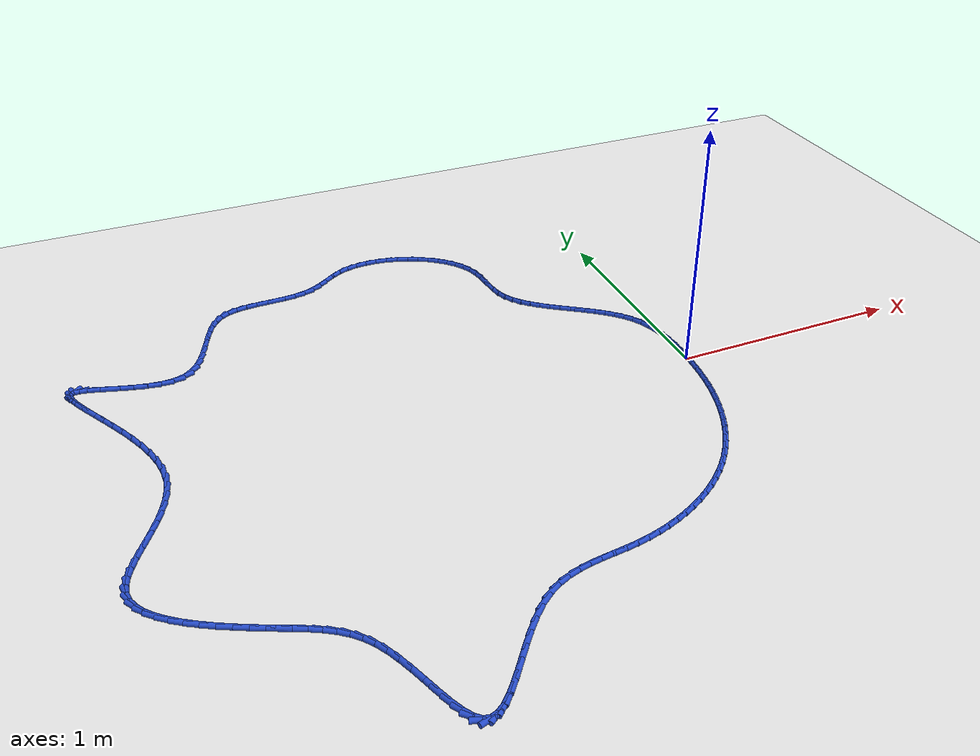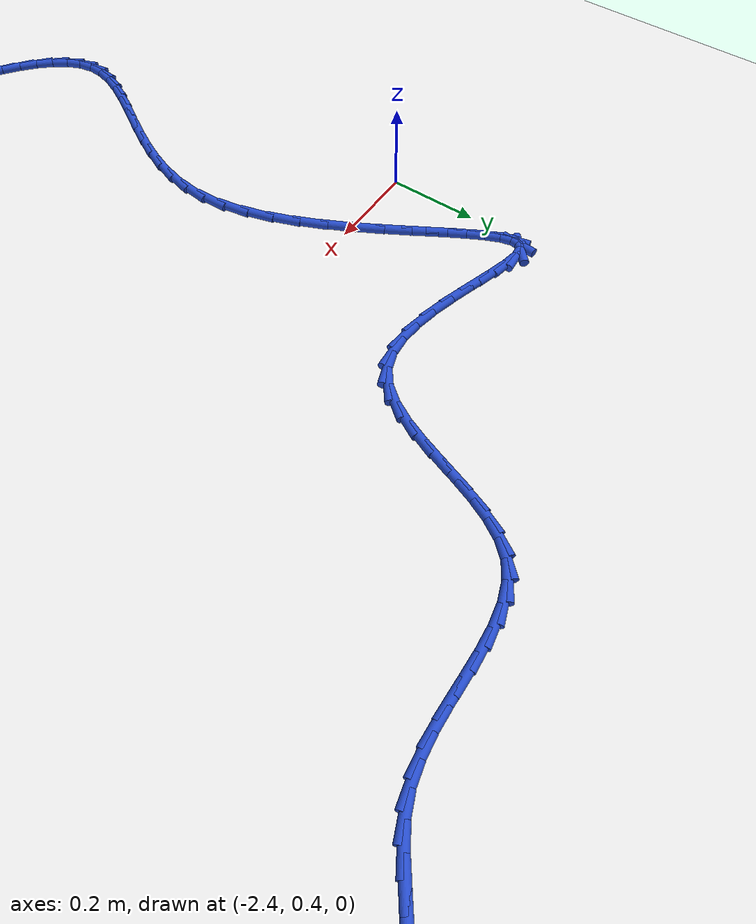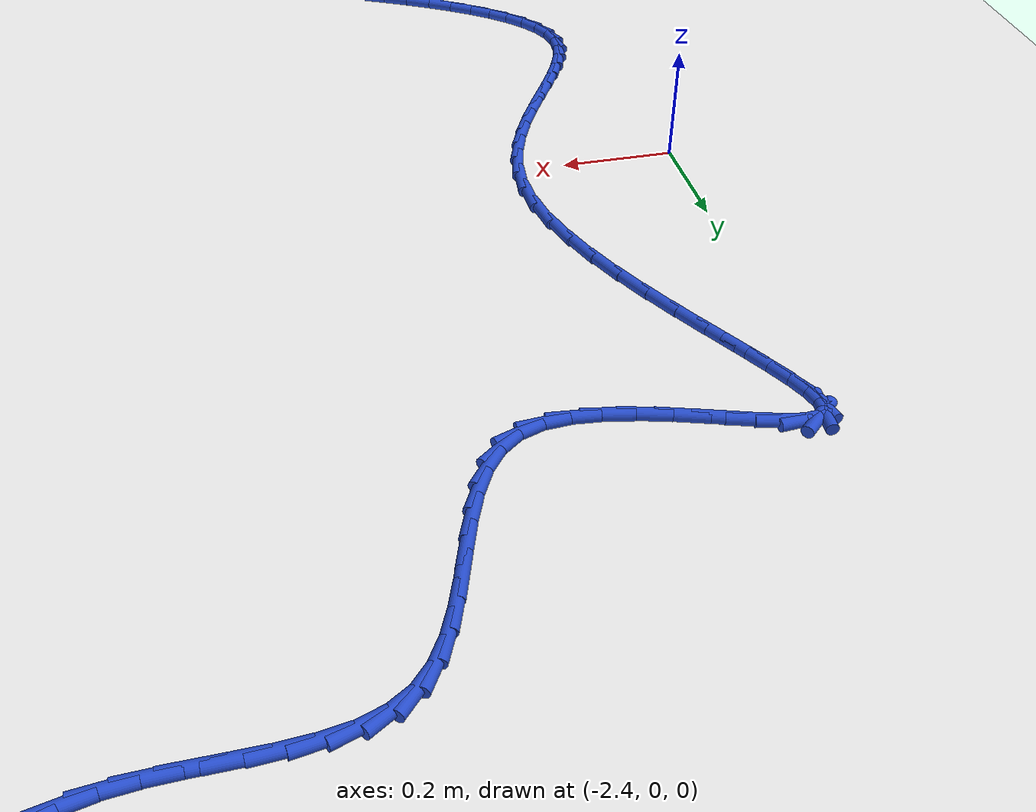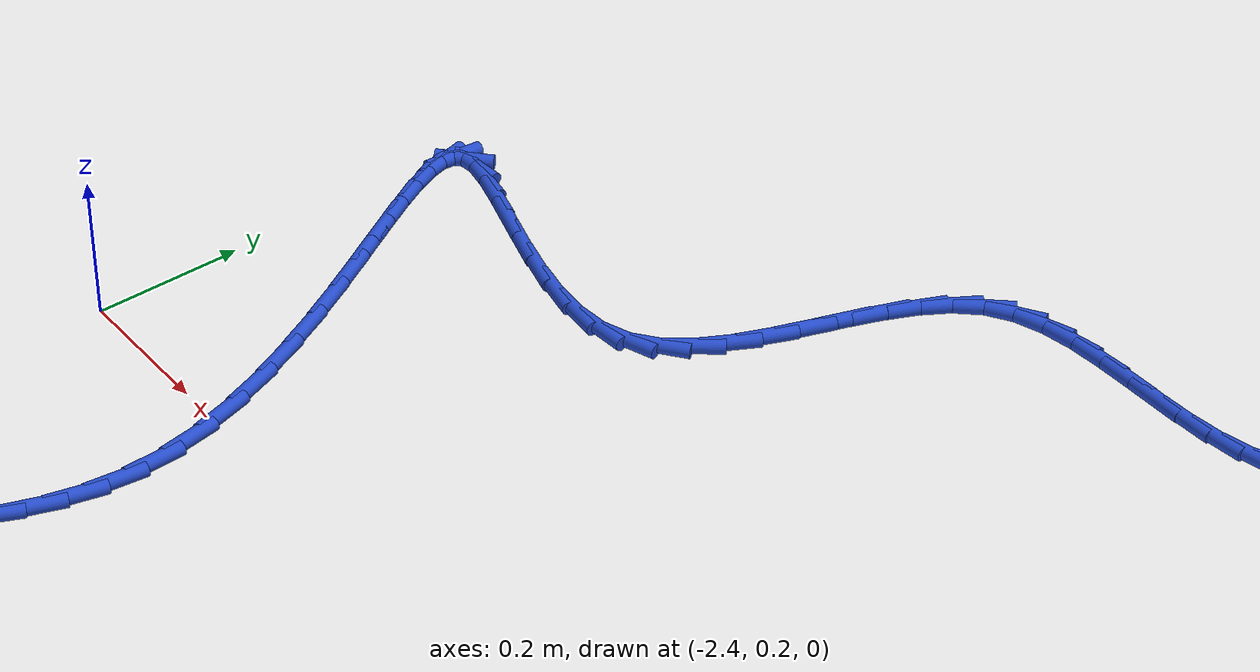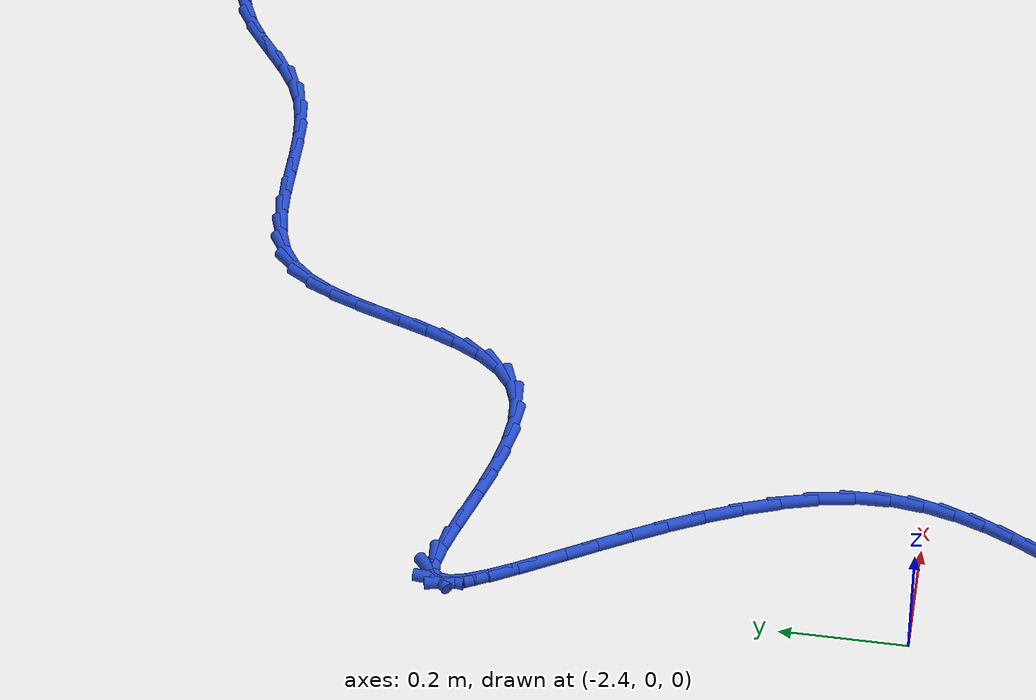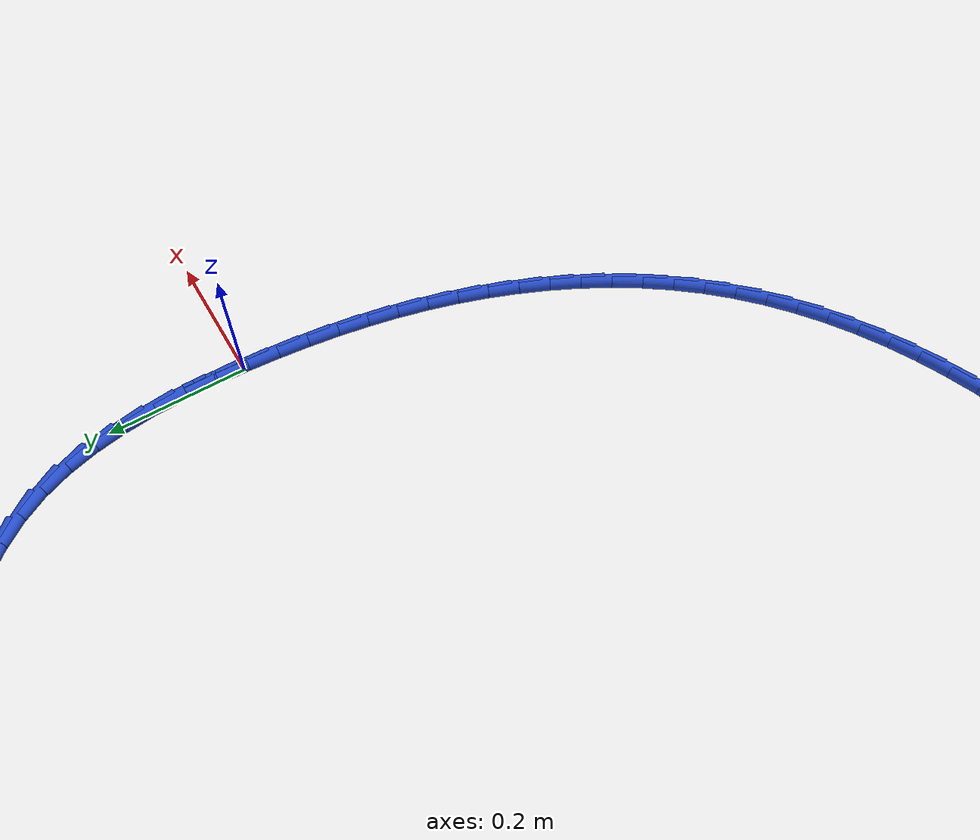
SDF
<sdf version="1.6">
 <world name="default">
  <light name="sun" type="directional">
   <pose>0 0 10 0 -0 0</pose>
   <diffuse>0.8 0.8 0.8 1</diffuse>
   <specular>0.2 0.2 0.2 1</specular>
   <attenuation>
    <range>1000</range>
    <constant>0.9</constant>
    <linear>0.01</linear>
    <quadratic>0.001</quadratic>
   </attenuation>
   <direction>-0.5 0.1 -0.9</direction>
  </light>
  <model name="ground_plane">
   <static>1</static>
   <link name="link">
    <collision name="collision">
     <geometry><plane><normal>0 0 1</normal><size>100 100</size></plane></geometry>
     <surface><friction><ode><mu>100</mu><mu2>50</mu2></ode></friction></surface>
    </collision>
    <visual name="visual">
     <cast_shadows>0</cast_shadows>
     <geometry><plane><normal>0 0 1</normal><size>100 100</size></plane></geometry>
     <material>
      <script><uri>file://media/materials/scripts/gazebo.material</uri><name>Gazebo/WhiteGlow</name></script>
     </material>
    </visual>
   </link>
  </model>
  <gravity>0 0 -9.8</gravity>
  <magnetic_field>6e-06 2.3e-05 -4.2e-05</magnetic_field>
  <atmosphere type="adiabatic"/>
  <physics name="default_physics" default="0" type="ode">
   <max_step_size>0.001</max_step_size>
   <real_time_factor>1</real_time_factor>
   <real_time_update_rate>1000</real_time_update_rate>
  </physics>
  <scene><ambient>0.4 0.4 0.4 1</ambient><background>0.7 0.7 0.7 1</background><shadows>1</shadows></scene>
  <spherical_coordinates>
   <surface_model>EARTH_WGS84</surface_model>
   <latitude_deg>0</latitude_deg>
   <longitude_deg>0</longitude_deg>
   <elevation>0</elevation>
   <heading_deg>0</heading_deg>
  </spherical_coordinates>
  <model name="line">
   <link name="link_0">
    <pose>2.168404344971009e-19 0.0 0.01 0 1.57 1.5390488957896642</pose>
    <collision name="collision">
     <geometry><cylinder><radius>0.01</radius><length>0.08</length></cylinder></geometry>
    </collision>
    <visual name="visual">
     <material>
      <script><name>Gazebo/Blue</name><uri>file://media/materials/scripts/gazebo.material</uri></script>
     </material>
     <geometry><cylinder><radius>0.01</radius><length>0.08</length></cylinder></geometry>
    </visual>
   </link>
   <link name="link_1">
    <pose>0.0014721222336362635 0.04635422678655623 0.01 0 1.57 -1.5658661433238312</pose>
    <collision name="collision">
     <geometry><cylinder><radius>0.01</radius><length>0.08</length></cylinder></geometry>
    </collision>
    <visual name="visual">
     <material>
      <script><name>Gazebo/Blue</name><uri>file://media/materials/scripts/gazebo.material</uri></script>
     </material>
     <geometry><cylinder><radius>0.01</radius><length>0.08</length></cylinder></geometry>
    </visual>
   </link>
   <link name="link_2">
    <pose>0.001242675760363433 0.09289298454006431 0.01 0 1.57 -1.5177054942123234</pose>
    <collision name="collision">
     <geometry><cylinder><radius>0.01</radius><length>0.08</length></cylinder></geometry>
    </collision>
    <visual name="visual">
     <material>
      <script><name>Gazebo/Blue</name><uri>file://media/materials/scripts/gazebo.material</uri></script>
     </material>
     <geometry><cylinder><radius>0.01</radius><length>0.08</length></cylinder></geometry>
    </visual>
   </link>
   <link name="link_3">
    <pose>-0.001215517973724256 0.1391511348769408 0.01 0 1.57 -1.4567288402673002</pose>
    <collision name="collision">
     <geometry><cylinder><radius>0.01</radius><length>0.08</length></cylinder></geometry>
    </collision>
    <visual name="visual">
     <material>
      <script><name>Gazebo/Blue</name><uri>file://media/materials/scripts/gazebo.material</uri></script>
     </material>
     <geometry><cylinder><radius>0.01</radius><length>0.08</length></cylinder></geometry>
    </visual>
   </link>
   <link name="link_4">
    <pose>-0.006429637522532561 0.18466353941360214 0.01 0 1.57 -1.3812934842537212</pose>
    <collision name="collision">
     <geometry><cylinder><radius>0.01</radius><length>0.08</length></cylinder></geometry>
    </collision>
    <visual name="visual">
     <material>
      <script><name>Gazebo/Blue</name><uri>file://media/materials/scripts/gazebo.material</uri></script>
     </material>
     <geometry><cylinder><radius>0.01</radius><length>0.08</length></cylinder></geometry>
    </visual>
   </link>
   <link name="link_5">
    <pose>-0.014926861439967248 0.22896505976646497 0.01 0 1.57 -1.2897054352338209</pose>
    <collision name="collision">
     <geometry><cylinder><radius>0.01</radius><length>0.08</length></cylinder></geometry>
    </collision>
    <visual name="visual">
     <material>
      <script><name>Gazebo/Blue</name><uri>file://media/materials/scripts/gazebo.material</uri></script>
     </material>
     <geometry><cylinder><radius>0.01</radius><length>0.08</length></cylinder></geometry>
    </visual>
   </link>
   <link name="link_6">
    <pose>-0.027234368279934064 0.2715905575519456 0.01 0 1.57 -1.1807185123168167</pose>
    <collision name="collision">
     <geometry><cylinder><radius>0.01</radius><length>0.08</length></cylinder></geometry>
    </collision>
    <visual name="visual">
     <material>
      <script><name>Gazebo/Blue</name><uri>file://media/materials/scripts/gazebo.material</uri></script>
     </material>
     <geometry><cylinder><radius>0.01</radius><length>0.08</length></cylinder></geometry>
    </visual>
   </link>
   <link name="link_7">
    <pose>-0.04387933659633879 0.31207489438646085 0.01 0 1.57 -1.0544038282959072</pose>
    <collision name="collision">
     <geometry><cylinder><radius>0.01</radius><length>0.08</length></cylinder></geometry>
    </collision>
    <visual name="visual">
     <material>
      <script><name>Gazebo/Blue</name><uri>file://media/materials/scripts/gazebo.material</uri></script>
     </material>
     <geometry><cylinder><radius>0.01</radius><length>0.08</length></cylinder></geometry>
    </visual>
   </link>
   <link name="link_8">
    <pose>-0.06538665243420566 0.3499544556711538 0.01 0 1.57 -0.9239087075336251</pose>
    <collision name="collision">
     <geometry><cylinder><radius>0.01</radius><length>0.08</length></cylinder></geometry>
    </collision>
    <visual name="visual">
     <material>
      <script><name>Gazebo/Blue</name><uri>file://media/materials/scripts/gazebo.material</uri></script>
     </material>
     <geometry><cylinder><radius>0.01</radius><length>0.08</length></cylinder></geometry>
    </visual>
   </link>
   <link name="link_9">
    <pose>-0.091880744946308 0.38503180248096447 0.01 0 1.57 -0.8152841722291819</pose>
    <collision name="collision">
     <geometry><cylinder><radius>0.01</radius><length>0.08</length></cylinder></geometry>
    </collision>
    <visual name="visual">
     <material>
      <script><name>Gazebo/Blue</name><uri>file://media/materials/scripts/gazebo.material</uri></script>
     </material>
     <geometry><cylinder><radius>0.01</radius><length>0.08</length></cylinder></geometry>
    </visual>
   </link>
   <link name="link_10">
    <pose>-0.12263132391835779 0.41767761073124665 0.01 0 1.57 -0.7313215988986559</pose>
    <collision name="collision">
     <geometry><cylinder><radius>0.01</radius><length>0.08</length></cylinder></geometry>
    </collision>
    <visual name="visual">
     <material>
      <script><name>Gazebo/Blue</name><uri>file://media/materials/scripts/gazebo.material</uri></script>
     </material>
     <geometry><cylinder><radius>0.01</radius><length>0.08</length></cylinder></geometry>
    </visual>
   </link>
   <link name="link_11">
    <pose>-0.1567982270477632 0.4483355861133468 0.01 0 1.57 -0.6700669063821367</pose>
    <collision name="collision">
     <geometry><cylinder><radius>0.01</radius><length>0.08</length></cylinder></geometry>
    </collision>
    <visual name="visual">
     <material>
      <script><name>Gazebo/Blue</name><uri>file://media/materials/scripts/gazebo.material</uri></script>
     </material>
     <geometry><cylinder><radius>0.01</radius><length>0.08</length></cylinder></geometry>
    </visual>
   </link>
   <link name="link_12">
    <pose>-0.19354129203193238 0.4774494343186114 0.01 0 1.57 -0.6292831395808915</pose>
    <collision name="collision">
     <geometry><cylinder><radius>0.01</radius><length>0.08</length></cylinder></geometry>
    </collision>
    <visual name="visual">
     <material>
      <script><name>Gazebo/Blue</name><uri>file://media/materials/scripts/gazebo.material</uri></script>
     </material>
     <geometry><cylinder><radius>0.01</radius><length>0.08</length></cylinder></geometry>
    </visual>
   </link>
   <link name="link_13">
    <pose>-0.23202035656827363 0.5054628610383869 0.01 0 1.57 -0.6072108702370764</pose>
    <collision name="collision">
     <geometry><cylinder><radius>0.01</radius><length>0.08</length></cylinder></geometry>
    </collision>
    <visual name="visual">
     <material>
      <script><name>Gazebo/Blue</name><uri>file://media/materials/scripts/gazebo.material</uri></script>
     </material>
     <geometry><cylinder><radius>0.01</radius><length>0.08</length></cylinder></geometry>
    </visual>
   </link>
   <link name="link_14">
    <pose>-0.27139525835419503 0.5328195719640196 0.01 0 1.57 -0.602892926813047</pose>
    <collision name="collision">
     <geometry><cylinder><radius>0.01</radius><length>0.08</length></cylinder></geometry>
    </collision>
    <visual name="visual">
     <material>
      <script><name>Gazebo/Blue</name><uri>file://media/materials/scripts/gazebo.material</uri></script>
     </material>
     <geometry><cylinder><radius>0.01</radius><length>0.08</length></cylinder></geometry>
    </visual>
   </link>
   <link name="link_15">
    <pose>-0.31082583508710493 0.5599632727868563 0.01 0 1.57 -0.6162983693012791</pose>
    <collision name="collision">
     <geometry><cylinder><radius>0.01</radius><length>0.08</length></cylinder></geometry>
    </collision>
    <visual name="visual">
     <material>
      <script><name>Gazebo/Blue</name><uri>file://media/materials/scripts/gazebo.material</uri></script>
     </material>
     <geometry><cylinder><radius>0.01</radius><length>0.08</length></cylinder></geometry>
    </visual>
   </link>
   <link name="link_16">
    <pose>-0.34947192446441117 0.5873376691982429 0.01 0 1.57 -0.648370644125655</pose>
    <collision name="collision">
     <geometry><cylinder><radius>0.01</radius><length>0.08</length></cylinder></geometry>
    </collision>
    <visual name="visual">
     <material>
      <script><name>Gazebo/Blue</name><uri>file://media/materials/scripts/gazebo.material</uri></script>
     </material>
     <geometry><cylinder><radius>0.01</radius><length>0.08</length></cylinder></geometry>
    </visual>
   </link>
   <link name="link_17">
    <pose>-0.3864933641835222 0.6153864668895259 0.01 0 1.57 -0.7010191977605005</pose>
    <collision name="collision">
     <geometry><cylinder><radius>0.01</radius><length>0.08</length></cylinder></geometry>
    </collision>
    <visual name="visual">
     <material>
      <script><name>Gazebo/Blue</name><uri>file://media/materials/scripts/gazebo.material</uri></script>
     </material>
     <geometry><cylinder><radius>0.01</radius><length>0.08</length></cylinder></geometry>
    </visual>
   </link>
   <link name="link_18">
    <pose>-0.42104999194184634 0.6445533715520524 0.01 0 1.57 -0.7769612380447642</pose>
    <collision name="collision">
     <geometry><cylinder><radius>0.01</radius><length>0.08</length></cylinder></geometry>
    </collision>
    <visual name="visual">
     <material>
      <script><name>Gazebo/Blue</name><uri>file://media/materials/scripts/gazebo.material</uri></script>
     </material>
     <geometry><cylinder><radius>0.01</radius><length>0.08</length></cylinder></geometry>
    </visual>
   </link>
   <link name="link_19">
    <pose>-0.4523016454367913 0.6752820888771678 0.01 0 1.57 -0.8791672863578113</pose>
    <collision name="collision">
     <geometry><cylinder><radius>0.01</radius><length>0.08</length></cylinder></geometry>
    </collision>
    <visual name="visual">
     <material>
      <script><name>Gazebo/Blue</name><uri>file://media/materials/scripts/gazebo.material</uri></script>
     </material>
     <geometry><cylinder><radius>0.01</radius><length>0.08</length></cylinder></geometry>
    </visual>
   </link>
   <link name="link_20">
    <pose>-0.4794081623657659 0.7080163245562194 0.01 0 1.57 -1.009512712170234</pose>
    <collision name="collision">
     <geometry><cylinder><radius>0.01</radius><length>0.08</length></cylinder></geometry>
    </collision>
    <visual name="visual">
     <material>
      <script><name>Gazebo/Blue</name><uri>file://media/materials/scripts/gazebo.material</uri></script>
     </material>
     <geometry><cylinder><radius>0.01</radius><length>0.08</length></cylinder></geometry>
    </visual>
   </link>
   <link name="link_21">
    <pose>-0.5015293804261778 0.7431997842805529 0.01 0 1.57 -1.166408215397185</pose>
    <collision name="collision">
     <geometry><cylinder><radius>0.01</radius><length>0.08</length></cylinder></geometry>
    </collision>
    <visual name="visual">
     <material>
      <script><name>Gazebo/Blue</name><uri>file://media/materials/scripts/gazebo.material</uri></script>
     </material>
     <geometry><cylinder><radius>0.01</radius><length>0.08</length></cylinder></geometry>
    </visual>
   </link>
   <link name="link_22">
    <pose>-0.5178251373161454 0.7812761737412091 0.01 0 1.57 -1.328679591865516</pose>
    <collision name="collision">
     <geometry><cylinder><radius>0.01</radius><length>0.08</length></cylinder></geometry>
    </collision>
    <visual name="visual">
     <material>
      <script><name>Gazebo/Blue</name><uri>file://media/materials/scripts/gazebo.material</uri></script>
     </material>
     <geometry><cylinder><radius>0.01</radius><length>0.08</length></cylinder></geometry>
    </visual>
   </link>
   <link name="link_23">
    <pose>-0.5279951064135744 0.8224565786669649 0.01 0 1.57 -1.4362827417552126</pose>
    <collision name="collision">
     <geometry><cylinder><radius>0.01</radius><length>0.08</length></cylinder></geometry>
    </collision>
    <visual name="visual">
     <material>
      <script><name>Gazebo/Blue</name><uri>file://media/materials/scripts/gazebo.material</uri></script>
     </material>
     <geometry><cylinder><radius>0.01</radius><length>0.08</length></cylinder></geometry>
    </visual>
   </link>
   <link name="link_24">
    <pose>-0.5338912096270387 0.866024661886013 0.01 0 1.57 -1.4819263324855885</pose>
    <collision name="collision">
     <geometry><cylinder><radius>0.01</radius><length>0.08</length></cylinder></geometry>
    </collision>
    <visual name="visual">
     <material>
      <script><name>Gazebo/Blue</name><uri>file://media/materials/scripts/gazebo.material</uri></script>
     </material>
     <geometry><cylinder><radius>0.01</radius><length>0.08</length></cylinder></geometry>
    </visual>
   </link>
   <link name="link_25">
    <pose>-0.5379016632734943 0.9110329922294088 0.01 0 1.57 -1.4719349049685204</pose>
    <collision name="collision">
     <geometry><cylinder><radius>0.01</radius><length>0.08</length></cylinder></geometry>
    </collision>
    <visual name="visual">
     <material>
      <script><name>Gazebo/Blue</name><uri>file://media/materials/scripts/gazebo.material</uri></script>
     </material>
     <geometry><cylinder><radius>0.01</radius><length>0.08</length></cylinder></geometry>
    </visual>
   </link>
   <link name="link_26">
    <pose>-0.5424146836698962 0.9565341385282068 0.01 0 1.57 -1.4078937691609754</pose>
    <collision name="collision">
     <geometry><cylinder><radius>0.01</radius><length>0.08</length></cylinder></geometry>
    </collision>
    <visual name="visual">
     <material>
      <script><name>Gazebo/Blue</name><uri>file://media/materials/scripts/gazebo.material</uri></script>
     </material>
     <geometry><cylinder><radius>0.01</radius><length>0.08</length></cylinder></geometry>
    </visual>
   </link>
   <link name="link_27">
    <pose>-0.5498184871332 1.0015806696134621 0.01 0 1.57 -1.2879919824715333</pose>
    <collision name="collision">
     <geometry><cylinder><radius>0.01</radius><length>0.08</length></cylinder></geometry>
    </collision>
    <visual name="visual">
     <material>
      <script><name>Gazebo/Blue</name><uri>file://media/materials/scripts/gazebo.material</uri></script>
     </material>
     <geometry><cylinder><radius>0.01</radius><length>0.08</length></cylinder></geometry>
    </visual>
   </link>
   <link name="link_28">
    <pose>-0.5625012705173579 1.0452251580667087 0.01 0 1.57 -1.125641293259757</pose>
    <collision name="collision">
     <geometry><cylinder><radius>0.01</radius><length>0.08</length></cylinder></geometry>
    </collision>
    <visual name="visual">
     <material>
      <script><name>Gazebo/Blue</name><uri>file://media/materials/scripts/gazebo.material</uri></script>
     </material>
     <geometry><cylinder><radius>0.01</radius><length>0.08</length></cylinder></geometry>
    </visual>
   </link>
   <link name="link_29">
    <pose>-0.5822574438572454 1.0866345979135643 0.01 0 1.57 -0.971526408927184</pose>
    <collision name="collision">
     <geometry><cylinder><radius>0.01</radius><length>0.08</length></cylinder></geometry>
    </collision>
    <visual name="visual">
     <material>
      <script><name>Gazebo/Blue</name><uri>file://media/materials/scripts/gazebo.material</uri></script>
     </material>
     <geometry><cylinder><radius>0.01</radius><length>0.08</length></cylinder></geometry>
    </visual>
   </link>
   <link name="link_30">
    <pose>-0.6087302687905483 1.1253905048533117 0.01 0 1.57 -0.835734269011406</pose>
    <collision name="collision">
     <geometry><cylinder><radius>0.01</radius><length>0.08</length></cylinder></geometry>
    </collision>
    <visual name="visual">
     <material>
      <script><name>Gazebo/Blue</name><uri>file://media/materials/scripts/gazebo.material</uri></script>
     </material>
     <geometry><cylinder><radius>0.01</radius><length>0.08</length></cylinder></geometry>
    </visual>
   </link>
   <link name="link_31">
    <pose>-0.6410760281235778 1.1611682343596013 0.01 0 1.57 -0.7153614754656391</pose>
    <collision name="collision">
     <geometry><cylinder><radius>0.01</radius><length>0.08</length></cylinder></geometry>
    </collision>
    <visual name="visual">
     <material>
      <script><name>Gazebo/Blue</name><uri>file://media/materials/scripts/gazebo.material</uri></script>
     </material>
     <geometry><cylinder><radius>0.01</radius><length>0.08</length></cylinder></geometry>
    </visual>
   </link>
   <link name="link_32">
    <pose>-0.6784510046626457 1.1936431419060827 0.01 0 1.57 -0.6067603509886731</pose>
    <collision name="collision">
     <geometry><cylinder><radius>0.01</radius><length>0.08</length></cylinder></geometry>
    </collision>
    <visual name="visual">
     <material>
      <script><name>Gazebo/Blue</name><uri>file://media/materials/scripts/gazebo.material</uri></script>
     </material>
     <geometry><cylinder><radius>0.01</radius><length>0.08</length></cylinder></geometry>
    </visual>
   </link>
   <link name="link_33">
    <pose>-0.7200114812140637 1.222490582966407 0.01 0 1.57 -0.5062409014885254</pose>
    <collision name="collision">
     <geometry><cylinder><radius>0.01</radius><length>0.08</length></cylinder></geometry>
    </collision>
    <visual name="visual">
     <material>
      <script><name>Gazebo/Blue</name><uri>file://media/materials/scripts/gazebo.material</uri></script>
     </material>
     <geometry><cylinder><radius>0.01</radius><length>0.08</length></cylinder></geometry>
    </visual>
   </link>
   <link name="link_34">
    <pose>-0.7649137405841424 1.2473859130142229 0.01 0 1.57 -0.41030009966259573</pose>
    <collision name="collision">
     <geometry><cylinder><radius>0.01</radius><length>0.08</length></cylinder></geometry>
    </collision>
    <visual name="visual">
     <material>
      <script><name>Gazebo/Blue</name><uri>file://media/materials/scripts/gazebo.material</uri></script>
     </material>
     <geometry><cylinder><radius>0.01</radius><length>0.08</length></cylinder></geometry>
    </visual>
   </link>
   <link name="link_35">
    <pose>-0.8123140655791941 1.2680044875231808 0.01 0 1.57 -0.3156031704391992</pose>
    <collision name="collision">
     <geometry><cylinder><radius>0.01</radius><length>0.08</length></cylinder></geometry>
    </collision>
    <visual name="visual">
     <material>
      <script><name>Gazebo/Blue</name><uri>file://media/materials/scripts/gazebo.material</uri></script>
     </material>
     <geometry><cylinder><radius>0.01</radius><length>0.08</length></cylinder></geometry>
    </visual>
   </link>
   <link name="link_36">
    <pose>-0.86136873900553 1.2840216619669313 0.01 0 1.57 -0.21885910520567317</pose>
    <collision name="collision">
     <geometry><cylinder><radius>0.01</radius><length>0.08</length></cylinder></geometry>
    </collision>
    <visual name="visual">
     <material>
      <script><name>Gazebo/Blue</name><uri>file://media/materials/scripts/gazebo.material</uri></script>
     </material>
     <geometry><cylinder><radius>0.01</radius><length>0.08</length></cylinder></geometry>
    </visual>
   </link>
   <link name="link_37">
    <pose>-0.9112340436694611 1.2951127918191232 0.01 0 1.57 -0.11666983870270584</pose>
    <collision name="collision">
     <geometry><cylinder><radius>0.01</radius><length>0.08</length></cylinder></geometry>
    </collision>
    <visual name="visual">
     <material>
      <script><name>Gazebo/Blue</name><uri>file://media/materials/scripts/gazebo.material</uri></script>
     </material>
     <geometry><cylinder><radius>0.01</radius><length>0.08</length></cylinder></geometry>
    </visual>
   </link>
   <link name="link_38">
    <pose>-0.9610662623772994 1.3009532325534081 0.01 0 1.57 -0.005415223129232277</pose>
    <collision name="collision">
     <geometry><cylinder><radius>0.01</radius><length>0.08</length></cylinder></geometry>
    </collision>
    <visual name="visual">
     <material>
      <script><name>Gazebo/Blue</name><uri>file://media/materials/scripts/gazebo.material</uri></script>
     </material>
     <geometry><cylinder><radius>0.01</radius><length>0.08</length></cylinder></geometry>
    </visual>
   </link>
   <link name="link_39">
    <pose>-1.0100216779353564 1.3012183396434345 0.01 0 1.57 0.11873354741328766</pose>
    <collision name="collision">
     <geometry><cylinder><radius>0.01</radius><length>0.08</length></cylinder></geometry>
    </collision>
    <visual name="visual">
     <material>
      <script><name>Gazebo/Blue</name><uri>file://media/materials/scripts/gazebo.material</uri></script>
     </material>
     <geometry><cylinder><radius>0.01</radius><length>0.08</length></cylinder></geometry>
    </visual>
   </link>
   <link name="link_40">
    <pose>-1.0572565731499435 1.2955834685628531 0.01 0 1.57 0.2595010313212118</pose>
    <collision name="collision">
     <geometry><cylinder><radius>0.01</radius><length>0.08</length></cylinder></geometry>
    </collision>
    <visual name="visual">
     <material>
      <script><name>Gazebo/Blue</name><uri>file://media/materials/scripts/gazebo.material</uri></script>
     </material>
     <geometry><cylinder><radius>0.01</radius><length>0.08</length></cylinder></geometry>
    </visual>
   </link>
   <link name="link_41">
    <pose>-1.1019272308273713 1.2837239747853137 0.01 0 1.57 0.41932412700191124</pose>
    <collision name="collision">
     <geometry><cylinder><radius>0.01</radius><length>0.08</length></cylinder></geometry>
    </collision>
    <visual name="visual">
     <material>
      <script><name>Gazebo/Blue</name><uri>file://media/materials/scripts/gazebo.material</uri></script>
     </material>
     <geometry><cylinder><radius>0.01</radius><length>0.08</length></cylinder></geometry>
    </visual>
   </link>
   <link name="link_42">
    <pose>-1.1431986052651588 1.2653267589906823 0.01 0 1.57 0.5669193455313425</pose>
    <collision name="collision">
     <geometry><cylinder><radius>0.01</radius><length>0.08</length></cylinder></geometry>
    </collision>
    <visual name="visual">
     <material>
      <script><name>Gazebo/Blue</name><uri>file://media/materials/scripts/gazebo.material</uri></script>
     </material>
     <geometry><cylinder><radius>0.01</radius><length>0.08</length></cylinder></geometry>
    </visual>
   </link>
   <link name="link_43">
    <pose>-1.1810837651608472 1.241207899691082 0.01 0 1.57 0.6420238794136489</pose>
    <collision name="collision">
     <geometry><cylinder><radius>0.01</radius><length>0.08</length></cylinder></geometry>
    </collision>
    <visual name="visual">
     <material>
      <script><name>Gazebo/Blue</name><uri>file://media/materials/scripts/gazebo.material</uri></script>
     </material>
     <geometry><cylinder><radius>0.01</radius><length>0.08</length></cylinder></geometry>
    </visual>
   </link>
   <link name="link_44">
    <pose>-1.2171445248463673 1.2142454722685305 0.01 0 1.57 0.6387863320301767</pose>
    <collision name="collision">
     <geometry><cylinder><radius>0.01</radius><length>0.08</length></cylinder></geometry>
    </collision>
    <visual name="visual">
     <material>
      <script><name>Gazebo/Blue</name><uri>file://media/materials/scripts/gazebo.material</uri></script>
     </material>
     <geometry><cylinder><radius>0.01</radius><length>0.08</length></cylinder></geometry>
    </visual>
   </link>
   <link name="link_45">
    <pose>-1.2531076323361956 1.1875371444832854 0.01 0 1.57 0.5559442815740465</pose>
    <collision name="collision">
     <geometry><cylinder><radius>0.01</radius><length>0.08</length></cylinder></geometry>
    </collision>
    <visual name="visual">
     <material>
      <script><name>Gazebo/Blue</name><uri>file://media/materials/scripts/gazebo.material</uri></script>
     </material>
     <geometry><cylinder><radius>0.01</radius><length>0.08</length></cylinder></geometry>
    </visual>
   </link>
   <link name="link_46">
    <pose>-1.29069983564481 1.164180584095607 0.01 0 1.57 0.39514696649424697</pose>
    <collision name="collision">
     <geometry><cylinder><radius>0.01</radius><length>0.08</length></cylinder></geometry>
    </collision>
    <visual name="visual">
     <material>
      <script><name>Gazebo/Blue</name><uri>file://media/materials/scripts/gazebo.material</uri></script>
     </material>
     <geometry><cylinder><radius>0.01</radius><length>0.08</length></cylinder></geometry>
    </visual>
   </link>
   <link name="link_47">
    <pose>-1.3315687215515852 1.1471348112035014 0.01 0 1.57 0.22806305997216328</pose>
    <collision name="collision">
     <geometry><cylinder><radius>0.01</radius><length>0.08</length></cylinder></geometry>
    </collision>
    <visual name="visual">
     <material>
      <script><name>Gazebo/Blue</name><uri>file://media/materials/scripts/gazebo.material</uri></script>
     </material>
     <geometry><cylinder><radius>0.01</radius><length>0.08</length></cylinder></geometry>
    </visual>
   </link>
   <link name="link_48">
    <pose>-1.3759237157967537 1.1368399657262411 0.01 0 1.57 0.11274368224410479</pose>
    <collision name="collision">
     <geometry><cylinder><radius>0.01</radius><length>0.08</length></cylinder></geometry>
    </collision>
    <visual name="visual">
     <material>
      <script><name>Gazebo/Blue</name><uri>file://media/materials/scripts/gazebo.material</uri></script>
     </material>
     <geometry><cylinder><radius>0.01</radius><length>0.08</length></cylinder></geometry>
    </visual>
   </link>
   <link name="link_49">
    <pose>-1.422721116077779 1.1315413851218772 0.01 0 1.57 0.044212919236985525</pose>
    <collision name="collision">
     <geometry><cylinder><radius>0.01</radius><length>0.08</length></cylinder></geometry>
    </collision>
    <visual name="visual">
     <material>
      <script><name>Gazebo/Blue</name><uri>file://media/materials/scripts/gazebo.material</uri></script>
     </material>
     <geometry><cylinder><radius>0.01</radius><length>0.08</length></cylinder></geometry>
    </visual>
   </link>
   <link name="link_50">
    <pose>-1.470875285632513 1.1294109603593367 0.01 0 1.57 0.01632014143880842</pose>
    <collision name="collision">
     <geometry><cylinder><radius>0.01</radius><length>0.08</length></cylinder></geometry>
    </collision>
    <visual name="visual">
     <material>
      <script><name>Gazebo/Blue</name><uri>file://media/materials/scripts/gazebo.material</uri></script>
     </material>
     <geometry><cylinder><radius>0.01</radius><length>0.08</length></cylinder></geometry>
    </visual>
   </link>
   <link name="link_51">
    <pose>-1.5193005876988095 1.1286205824075486 0.01 0 1.57 0.02684544476173339</pose>
    <collision name="collision">
     <geometry><cylinder><radius>0.01</radius><length>0.08</length></cylinder></geometry>
    </collision>
    <visual name="visual">
     <material>
      <script><name>Gazebo/Blue</name><uri>file://media/materials/scripts/gazebo.material</uri></script>
     </material>
     <geometry><cylinder><radius>0.01</radius><length>0.08</length></cylinder></geometry>
    </visual>
   </link>
   <link name="link_52">
    <pose>-1.5669113855145214 1.1273421422354404 0.01 0 1.57 0.07847686650420913</pose>
    <collision name="collision">
     <geometry><cylinder><radius>0.01</radius><length>0.08</length></cylinder></geometry>
    </collision>
    <visual name="visual">
     <material>
      <script><name>Gazebo/Blue</name><uri>file://media/materials/scripts/gazebo.material</uri></script>
     </material>
     <geometry><cylinder><radius>0.01</radius><length>0.08</length></cylinder></geometry>
    </visual>
   </link>
   <link name="link_53">
    <pose>-1.612622042317501 1.1237475308119411 0.01 0 1.57 0.17919030424201426</pose>
    <collision name="collision">
     <geometry><cylinder><radius>0.01</radius><length>0.08</length></cylinder></geometry>
    </collision>
    <visual name="visual">
     <material>
      <script><name>Gazebo/Blue</name><uri>file://media/materials/scripts/gazebo.material</uri></script>
     </material>
     <geometry><cylinder><radius>0.01</radius><length>0.08</length></cylinder></geometry>
    </visual>
   </link>
   <link name="link_54">
    <pose>-1.6553469213456027 1.1160086391059783 0.01 0 1.57 0.3408763668120816</pose>
    <collision name="collision">
     <geometry><cylinder><radius>0.01</radius><length>0.08</length></cylinder></geometry>
    </collision>
    <visual name="visual">
     <material>
      <script><name>Gazebo/Blue</name><uri>file://media/materials/scripts/gazebo.material</uri></script>
     </material>
     <geometry><cylinder><radius>0.01</radius><length>0.08</length></cylinder></geometry>
    </visual>
   </link>
   <link name="link_55">
    <pose>-1.6940003858366783 1.1022973580864803 0.01 0 1.57 0.5708767688914463</pose>
    <collision name="collision">
     <geometry><cylinder><radius>0.01</radius><length>0.08</length></cylinder></geometry>
    </collision>
    <visual name="visual">
     <material>
      <script><name>Gazebo/Blue</name><uri>file://media/materials/scripts/gazebo.material</uri></script>
     </material>
     <geometry><cylinder><radius>0.01</radius><length>0.08</length></cylinder></geometry>
    </visual>
   </link>
   <link name="link_56">
    <pose>-1.7274968765824859 1.0807857030864998 0.01 0 1.57 0.8310854247131998</pose>
    <collision name="collision">
     <geometry><cylinder><radius>0.01</radius><length>0.08</length></cylinder></geometry>
    </collision>
    <visual name="visual">
     <material>
      <script><name>Gazebo/Blue</name><uri>file://media/materials/scripts/gazebo.material</uri></script>
     </material>
     <geometry><cylinder><radius>0.01</radius><length>0.08</length></cylinder></geometry>
    </visual>
   </link>
   <link name="link_57">
    <pose>-1.755223017300985 1.0504028739626246 0.01 0 1.57 1.025249480476236</pose>
    <collision name="collision">
     <geometry><cylinder><radius>0.01</radius><length>0.08</length></cylinder></geometry>
    </collision>
    <visual name="visual">
     <material>
      <script><name>Gazebo/Blue</name><uri>file://media/materials/scripts/gazebo.material</uri></script>
     </material>
     <geometry><cylinder><radius>0.01</radius><length>0.08</length></cylinder></geometry>
    </visual>
   </link>
   <link name="link_58">
    <pose>-1.7781538494545799 1.0126252302975927 0.01 0 1.57 1.1475236895543983</pose>
    <collision name="collision">
     <geometry><cylinder><radius>0.01</radius><length>0.08</length></cylinder></geometry>
    </collision>
    <visual name="visual">
     <material>
      <script><name>Gazebo/Blue</name><uri>file://media/materials/scripts/gazebo.material</uri></script>
     </material>
     <geometry><cylinder><radius>0.01</radius><length>0.08</length></cylinder></geometry>
    </visual>
   </link>
   <link name="link_59">
    <pose>-1.7975980639612406 0.9694641662762494 0.01 0 1.57 1.2154896711996002</pose>
    <collision name="collision">
     <geometry><cylinder><radius>0.01</radius><length>0.08</length></cylinder></geometry>
    </collision>
    <visual name="visual">
     <material>
      <script><name>Gazebo/Blue</name><uri>file://media/materials/scripts/gazebo.material</uri></script>
     </material>
     <geometry><cylinder><radius>0.01</radius><length>0.08</length></cylinder></geometry>
    </visual>
   </link>
   <link name="link_60">
    <pose>-1.8148643517389391 0.9229310760834392 0.01 0 1.57 1.2409409513675356</pose>
    <collision name="collision">
     <geometry><cylinder><radius>0.01</radius><length>0.08</length></cylinder></geometry>
    </collision>
    <visual name="visual">
     <material>
      <script><name>Gazebo/Blue</name><uri>file://media/materials/scripts/gazebo.material</uri></script>
     </material>
     <geometry><cylinder><radius>0.01</radius><length>0.08</length></cylinder></geometry>
    </visual>
   </link>
   <link name="link_61">
    <pose>-1.8312614037056454 0.8750373539040065 0.01 0 1.57 1.228447965268901</pose>
    <collision name="collision">
     <geometry><cylinder><radius>0.01</radius><length>0.08</length></cylinder></geometry>
    </collision>
    <visual name="visual">
     <material>
      <script><name>Gazebo/Blue</name><uri>file://media/materials/scripts/gazebo.material</uri></script>
     </material>
     <geometry><cylinder><radius>0.01</radius><length>0.08</length></cylinder></geometry>
    </visual>
   </link>
   <link name="link_62">
    <pose>-1.8480979107793316 0.8277943939227962 0.01 0 1.57 1.1758271206886997</pose>
    <collision name="collision">
     <geometry><cylinder><radius>0.01</radius><length>0.08</length></cylinder></geometry>
    </collision>
    <visual name="visual">
     <material>
      <script><name>Gazebo/Blue</name><uri>file://media/materials/scripts/gazebo.material</uri></script>
     </material>
     <geometry><cylinder><radius>0.01</radius><length>0.08</length></cylinder></geometry>
    </visual>
   </link>
   <link name="link_63">
    <pose>-1.8666825638779678 0.783213590324652 0.01 0 1.57 1.0738881686351627</pose>
    <collision name="collision">
     <geometry><cylinder><radius>0.01</radius><length>0.08</length></cylinder></geometry>
    </collision>
    <visual name="visual">
     <material>
      <script><name>Gazebo/Blue</name><uri>file://media/materials/scripts/gazebo.material</uri></script>
     </material>
     <geometry><cylinder><radius>0.01</radius><length>0.08</length></cylinder></geometry>
    </visual>
   </link>
   <link name="link_64">
    <pose>-1.888324053919527 0.7433063372944199 0.01 0 1.57 0.9066204304446323</pose>
    <collision name="collision">
     <geometry><cylinder><radius>0.01</radius><length>0.08</length></cylinder></geometry>
    </collision>
    <visual name="visual">
     <material>
      <script><name>Gazebo/Blue</name><uri>file://media/materials/scripts/gazebo.material</uri></script>
     </material>
     <geometry><cylinder><radius>0.01</radius><length>0.08</length></cylinder></geometry>
    </visual>
   </link>
   <link name="link_65">
    <pose>-1.9143310718219775 0.7100840290169437 0.01 0 1.57 0.6587776222680009</pose>
    <collision name="collision">
     <geometry><cylinder><radius>0.01</radius><length>0.08</length></cylinder></geometry>
    </collision>
    <visual name="visual">
     <material>
      <script><name>Gazebo/Blue</name><uri>file://media/materials/scripts/gazebo.material</uri></script>
     </material>
     <geometry><cylinder><radius>0.01</radius><length>0.08</length></cylinder></geometry>
    </visual>
   </link>
   <link name="link_66">
    <pose>-1.9460123085032934 0.685558059677068 0.01 0 1.57 0.3470764764544963</pose>
    <collision name="collision">
     <geometry><cylinder><radius>0.01</radius><length>0.08</length></cylinder></geometry>
    </collision>
    <visual name="visual">
     <material>
      <script><name>Gazebo/Blue</name><uri>file://media/materials/scripts/gazebo.material</uri></script>
     </material>
     <geometry><cylinder><radius>0.01</radius><length>0.08</length></cylinder></geometry>
    </visual>
   </link>
   <link name="link_67">
    <pose>-1.9845731536030473 0.6716098714127785 0.01 0 1.57 0.08228906418897834</pose>
    <collision name="collision">
     <geometry><cylinder><radius>0.01</radius><length>0.08</length></cylinder></geometry>
    </collision>
    <visual name="visual">
     <material>
      <script><name>Gazebo/Blue</name><uri>file://media/materials/scripts/gazebo.material</uri></script>
     </material>
     <geometry><cylinder><radius>0.01</radius><length>0.08</length></cylinder></geometry>
    </visual>
   </link>
   <link name="link_68">
    <pose>-2.0294597837322983 0.6679078327441456 0.01 0 1.57 -0.08841369007323066</pose>
    <collision name="collision">
     <geometry><cylinder><radius>0.01</radius><length>0.08</length></cylinder></geometry>
    </collision>
    <visual name="visual">
     <material>
      <script><name>Gazebo/Blue</name><uri>file://media/materials/scripts/gazebo.material</uri></script>
     </material>
     <geometry><cylinder><radius>0.01</radius><length>0.08</length></cylinder></geometry>
    </visual>
   </link>
   <link name="link_69">
    <pose>-2.078645877693627 0.6722679236518389 0.01 0 1.57 -0.1954934567122599</pose>
    <collision name="collision">
     <geometry><cylinder><radius>0.01</radius><length>0.08</length></cylinder></geometry>
    </collision>
    <visual name="visual">
     <material>
      <script><name>Gazebo/Blue</name><uri>file://media/materials/scripts/gazebo.material</uri></script>
     </material>
     <geometry><cylinder><radius>0.01</radius><length>0.08</length></cylinder></geometry>
    </visual>
   </link>
   <link name="link_70">
    <pose>-2.1300597256004714 0.682449025567996 0.01 0 1.57 -0.26076573803681447</pose>
    <collision name="collision">
     <geometry><cylinder><radius>0.01</radius><length>0.08</length></cylinder></geometry>
    </collision>
    <visual name="visual">
     <material>
      <script><name>Gazebo/Blue</name><uri>file://media/materials/scripts/gazebo.material</uri></script>
     </material>
     <geometry><cylinder><radius>0.01</radius><length>0.08</length></cylinder></geometry>
    </visual>
   </link>
   <link name="link_71">
    <pose>-2.181629617566272 0.6962100199247556 0.01 0 1.57 -0.29521249437195773</pose>
    <collision name="collision">
     <geometry><cylinder><radius>0.01</radius><length>0.08</length></cylinder></geometry>
    </collision>
    <visual name="visual">
     <material>
      <script><name>Gazebo/Blue</name><uri>file://media/materials/scripts/gazebo.material</uri></script>
     </material>
     <geometry><cylinder><radius>0.01</radius><length>0.08</length></cylinder></geometry>
    </visual>
   </link>
   <link name="link_72">
    <pose>-2.2312838437044666 0.7113097881542555 0.01 0 1.57 -0.30141856154838353</pose>
    <collision name="collision">
     <geometry><cylinder><radius>0.01</radius><length>0.08</length></cylinder></geometry>
    </collision>
    <visual name="visual">
     <material>
      <script><name>Gazebo/Blue</name><uri>file://media/materials/scripts/gazebo.material</uri></script>
     </material>
     <geometry><cylinder><radius>0.01</radius><length>0.08</length></cylinder></geometry>
    </visual>
   </link>
   <link name="link_73">
    <pose>-2.2769506941284967 0.7255072116886339 0.01 0 1.57 -0.272160660149277</pose>
    <collision name="collision">
     <geometry><cylinder><radius>0.01</radius><length>0.08</length></cylinder></geometry>
    </collision>
    <visual name="visual">
     <material>
      <script><name>Gazebo/Blue</name><uri>file://media/materials/scripts/gazebo.material</uri></script>
     </material>
     <geometry><cylinder><radius>0.01</radius><length>0.08</length></cylinder></geometry>
    </visual>
   </link>
   <link name="link_74">
    <pose>-2.3165584589518016 0.736561171960029 0.01 0 1.57 -0.17820137625461402</pose>
    <collision name="collision">
     <geometry><cylinder><radius>0.01</radius><length>0.08</length></cylinder></geometry>
    </collision>
    <visual name="visual">
     <material>
      <script><name>Gazebo/Blue</name><uri>file://media/materials/scripts/gazebo.material</uri></script>
     </material>
     <geometry><cylinder><radius>0.01</radius><length>0.08</length></cylinder></geometry>
    </visual>
   </link>
   <link name="link_75">
    <pose>-2.3480354282878197 0.7422305504005786 0.01 0 1.57 0.08758824292946076</pose>
    <collision name="collision">
     <geometry><cylinder><radius>0.01</radius><length>0.08</length></cylinder></geometry>
    </collision>
    <visual name="visual">
     <material>
      <script><name>Gazebo/Blue</name><uri>file://media/materials/scripts/gazebo.material</uri></script>
     </material>
     <geometry><cylinder><radius>0.01</radius><length>0.08</length></cylinder></geometry>
    </visual>
   </link>
   <link name="link_76">
    <pose>-2.3694001777182203 0.7403544494537513 0.01 0 1.57 0.7454245299610825</pose>
    <collision name="collision">
     <geometry><cylinder><radius>0.01</radius><length>0.08</length></cylinder></geometry>
    </collision>
    <visual name="visual">
     <material>
      <script><name>Gazebo/Blue</name><uri>file://media/materials/scripts/gazebo.material</uri></script>
     </material>
     <geometry><cylinder><radius>0.01</radius><length>0.08</length></cylinder></geometry>
    </visual>
   </link>
   <link name="link_77">
    <pose>-2.380340761166525 0.7302553469456153 0.01 0 1.57 1.4764117641267474</pose>
    <collision name="collision">
     <geometry><cylinder><radius>0.01</radius><length>0.08</length></cylinder></geometry>
    </collision>
    <visual name="visual">
     <material>
      <script><name>Gazebo/Blue</name><uri>file://media/materials/scripts/gazebo.material</uri></script>
     </material>
     <geometry><cylinder><radius>0.01</radius><length>0.08</length></cylinder></geometry>
    </visual>
   </link>
   <link name="link_78">
    <pose>-2.3820156918439466 0.7125622624247613 0.01 0 1.57 -1.3170961937551722</pose>
    <collision name="collision">
     <geometry><cylinder><radius>0.01</radius><length>0.08</length></cylinder></geometry>
    </collision>
    <visual name="visual">
     <material>
      <script><name>Gazebo/Blue</name><uri>file://media/materials/scripts/gazebo.material</uri></script>
     </material>
     <geometry><cylinder><radius>0.01</radius><length>0.08</length></cylinder></geometry>
    </visual>
   </link>
   <link name="link_79">
    <pose>-2.3756337634605607 0.6879488909844502 0.01 0 1.57 -1.165786960549722</pose>
    <collision name="collision">
     <geometry><cylinder><radius>0.01</radius><length>0.08</length></cylinder></geometry>
    </collision>
    <visual name="visual">
     <material>
      <script><name>Gazebo/Blue</name><uri>file://media/materials/scripts/gazebo.material</uri></script>
     </material>
     <geometry><cylinder><radius>0.01</radius><length>0.08</length></cylinder></geometry>
    </visual>
   </link>
   <link name="link_80">
    <pose>-2.3624037697264453 0.6570889277179441 0.01 0 1.57 -1.0929166057188233</pose>
    <collision name="collision">
     <geometry><cylinder><radius>0.01</radius><length>0.08</length></cylinder></geometry>
    </collision>
    <visual name="visual">
     <material>
      <script><name>Gazebo/Blue</name><uri>file://media/materials/scripts/gazebo.material</uri></script>
     </material>
     <geometry><cylinder><radius>0.01</radius><length>0.08</length></cylinder></geometry>
    </visual>
   </link>
   <link name="link_81">
    <pose>-2.343534504351676 0.6206560677185053 0.01 0 1.57 -1.0574799686577696</pose>
    <collision name="collision">
     <geometry><cylinder><radius>0.01</radius><length>0.08</length></cylinder></geometry>
    </collision>
    <visual name="visual">
     <material>
      <script><name>Gazebo/Blue</name><uri>file://media/materials/scripts/gazebo.material</uri></script>
     </material>
     <geometry><cylinder><radius>0.01</radius><length>0.08</length></cylinder></geometry>
    </visual>
   </link>
   <link name="link_82">
    <pose>-2.3202347610463314 0.5793240060793958 0.01 0 1.57 -1.0436037721691385</pose>
    <collision name="collision">
     <geometry><cylinder><radius>0.01</radius><length>0.08</length></cylinder></geometry>
    </collision>
    <visual name="visual">
     <material>
      <script><name>Gazebo/Blue</name><uri>file://media/materials/scripts/gazebo.material</uri></script>
     </material>
     <geometry><cylinder><radius>0.01</radius><length>0.08</length></cylinder></geometry>
    </visual>
   </link>
   <link name="link_83">
    <pose>-2.2937133335204867 0.5337664378938763 0.01 0 1.57 -1.0444376567523979</pose>
    <collision name="collision">
     <geometry><cylinder><radius>0.01</radius><length>0.08</length></cylinder></geometry>
    </collision>
    <visual name="visual">
     <material>
      <script><name>Gazebo/Blue</name><uri>file://media/materials/scripts/gazebo.material</uri></script>
     </material>
     <geometry><cylinder><radius>0.01</radius><length>0.08</length></cylinder></geometry>
    </visual>
   </link>
   <link name="link_84">
    <pose>-2.26517901548422 0.4846570582552102 0.01 0 1.57 -1.057013264763882</pose>
    <collision name="collision">
     <geometry><cylinder><radius>0.01</radius><length>0.08</length></cylinder></geometry>
    </collision>
    <visual name="visual">
     <material>
      <script><name>Gazebo/Blue</name><uri>file://media/materials/scripts/gazebo.material</uri></script>
     </material>
     <geometry><cylinder><radius>0.01</radius><length>0.08</length></cylinder></geometry>
    </visual>
   </link>
   <link name="link_85">
    <pose>-2.2358406006476073 0.43266956225665837 0.01 0 1.57 -1.0803885467425383</pose>
    <collision name="collision">
     <geometry><cylinder><radius>0.01</radius><length>0.08</length></cylinder></geometry>
    </collision>
    <visual name="visual">
     <material>
      <script><name>Gazebo/Blue</name><uri>file://media/materials/scripts/gazebo.material</uri></script>
     </material>
     <geometry><cylinder><radius>0.01</radius><length>0.08</length></cylinder></geometry>
    </visual>
   </link>
   <link name="link_86">
    <pose>-2.2069068827207263 0.37847764499148345 0.01 0 1.57 -1.1149472467884982</pose>
    <collision name="collision">
     <geometry><cylinder><radius>0.01</radius><length>0.08</length></cylinder></geometry>
    </collision>
    <visual name="visual">
     <material>
      <script><name>Gazebo/Blue</name><uri>file://media/materials/scripts/gazebo.material</uri></script>
     </material>
     <geometry><cylinder><radius>0.01</radius><length>0.08</length></cylinder></geometry>
    </visual>
   </link>
   <link name="link_87">
    <pose>-2.179586655413653 0.32275500155294695 0.01 0 1.57 -1.1621848866673345</pose>
    <collision name="collision">
     <geometry><cylinder><radius>0.01</radius><length>0.08</length></cylinder></geometry>
    </collision>
    <visual name="visual">
     <material>
      <script><name>Gazebo/Blue</name><uri>file://media/materials/scripts/gazebo.material</uri></script>
     </material>
     <geometry><cylinder><radius>0.01</radius><length>0.08</length></cylinder></geometry>
    </visual>
   </link>
   <link name="link_88">
    <pose>-2.1550887124364646 0.26617532703431024 0.01 0 1.57 -1.2247389434740201</pose>
    <collision name="collision">
     <geometry><cylinder><radius>0.01</radius><length>0.08</length></cylinder></geometry>
    </collision>
    <visual name="visual">
     <material>
      <script><name>Gazebo/Blue</name><uri>file://media/materials/scripts/gazebo.material</uri></script>
     </material>
     <geometry><cylinder><radius>0.01</radius><length>0.08</length></cylinder></geometry>
    </visual>
   </link>
   <link name="link_89">
    <pose>-2.1346218474992384 0.2094123165288363 0.01 0 1.57 -1.3065317409505903</pose>
    <collision name="collision">
     <geometry><cylinder><radius>0.01</radius><length>0.08</length></cylinder></geometry>
    </collision>
    <visual name="visual">
     <material>
      <script><name>Gazebo/Blue</name><uri>file://media/materials/scripts/gazebo.material</uri></script>
     </material>
     <geometry><cylinder><radius>0.01</radius><length>0.08</length></cylinder></geometry>
    </visual>
   </link>
   <link name="link_90">
    <pose>-2.119394854312051 0.1531396651297865 0.01 0 1.57 -1.4128320158770638</pose>
    <collision name="collision">
     <geometry><cylinder><radius>0.01</radius><length>0.08</length></cylinder></geometry>
    </collision>
    <visual name="visual">
     <material>
      <script><name>Gazebo/Blue</name><uri>file://media/materials/scripts/gazebo.material</uri></script>
     </material>
     <geometry><cylinder><radius>0.01</radius><length>0.08</length></cylinder></geometry>
    </visual>
   </link>
   <link name="link_91">
    <pose>-2.1106165265849794 0.09803106793042268 0.01 0 1.57 -1.5484290151793105</pose>
    <collision name="collision">
     <geometry><cylinder><radius>0.01</radius><length>0.08</length></cylinder></geometry>
    </collision>
    <visual name="visual">
     <material>
      <script><name>Gazebo/Blue</name><uri>file://media/materials/scripts/gazebo.material</uri></script>
     </material>
     <geometry><cylinder><radius>0.01</radius><length>0.08</length></cylinder></geometry>
    </visual>
   </link>
   <link name="link_92">
    <pose>-2.109424316249901 0.04473849842858475 0.01 0 1.57 1.4494835203941077</pose>
    <collision name="collision">
     <geometry><cylinder><radius>0.01</radius><length>0.08</length></cylinder></geometry>
    </collision>
    <visual name="visual">
     <material>
      <script><name>Gazebo/Blue</name><uri>file://media/materials/scripts/gazebo.material</uri></script>
     </material>
     <geometry><cylinder><radius>0.01</radius><length>0.08</length></cylinder></geometry>
    </visual>
   </link>
   <link name="link_93">
    <pose>-2.1156682019725976 -0.006478069826683673 0.01 0 1.57 1.3237625167590295</pose>
    <collision name="collision">
     <geometry><cylinder><radius>0.01</radius><length>0.08</length></cylinder></geometry>
    </collision>
    <visual name="visual">
     <material>
      <script><name>Gazebo/Blue</name><uri>file://media/materials/scripts/gazebo.material</uri></script>
     </material>
     <geometry><cylinder><radius>0.01</radius><length>0.08</length></cylinder></geometry>
    </visual>
   </link>
   <link name="link_94">
    <pose>-2.1280809257794284 -0.0556988308975726 0.01 0 1.57 1.2206960666400923</pose>
    <collision name="collision">
     <geometry><cylinder><radius>0.01</radius><length>0.08</length></cylinder></geometry>
    </collision>
    <visual name="visual">
     <material>
      <script><name>Gazebo/Blue</name><uri>file://media/materials/scripts/gazebo.material</uri></script>
     </material>
     <geometry><cylinder><radius>0.01</radius><length>0.08</length></cylinder></geometry>
    </visual>
   </link>
   <link name="link_95">
    <pose>-2.1453581500647187 -0.10301526856718528 0.01 0 1.57 1.1413687843627698</pose>
    <collision name="collision">
     <geometry><cylinder><radius>0.01</radius><length>0.08</length></cylinder></geometry>
    </collision>
    <visual name="visual">
     <material>
      <script><name>Gazebo/Blue</name><uri>file://media/materials/scripts/gazebo.material</uri></script>
     </material>
     <geometry><cylinder><radius>0.01</radius><length>0.08</length></cylinder></geometry>
    </visual>
   </link>
   <link name="link_96">
    <pose>-2.1661955372227935 -0.14851886661862504 0.01 0 1.57 1.0854258324869326</pose>
    <collision name="collision">
     <geometry><cylinder><radius>0.01</radius><length>0.08</length></cylinder></geometry>
    </collision>
    <visual name="visual">
     <material>
      <script><name>Gazebo/Blue</name><uri>file://media/materials/scripts/gazebo.material</uri></script>
     </material>
     <geometry><cylinder><radius>0.01</radius><length>0.08</length></cylinder></geometry>
    </visual>
   </link>
   <link name="link_97">
    <pose>-2.189288749647978 -0.1923011088349951 0.01 0 1.57 1.0524082534120534</pose>
    <collision name="collision">
     <geometry><cylinder><radius>0.01</radius><length>0.08</length></cylinder></geometry>
    </collision>
    <visual name="visual">
     <material>
      <script><name>Gazebo/Blue</name><uri>file://media/materials/scripts/gazebo.material</uri></script>
     </material>
     <geometry><cylinder><radius>0.01</radius><length>0.08</length></cylinder></geometry>
    </visual>
   </link>
   <link name="link_98">
    <pose>-2.2133334497345962 -0.23445347899939953 0.01 0 1.57 1.0427152519622107</pose>
    <collision name="collision">
     <geometry><cylinder><radius>0.01</radius><length>0.08</length></cylinder></geometry>
    </collision>
    <visual name="visual">
     <material>
      <script><name>Gazebo/Blue</name><uri>file://media/materials/scripts/gazebo.material</uri></script>
     </material>
     <geometry><cylinder><radius>0.01</radius><length>0.08</length></cylinder></geometry>
    </visual>
   </link>
   <link name="link_99">
    <pose>-2.237025299876973 -0.27506746089494005 0.01 0 1.57 1.0583451626000282</pose>
    <collision name="collision">
     <geometry><cylinder><radius>0.01</radius><length>0.08</length></cylinder></geometry>
    </collision>
    <visual name="visual">
     <material>
      <script><name>Gazebo/Blue</name><uri>file://media/materials/scripts/gazebo.material</uri></script>
     </material>
     <geometry><cylinder><radius>0.01</radius><length>0.08</length></cylinder></geometry>
    </visual>
   </link>
   <link name="link_100">
    <pose>-2.2590599624694354 -0.3142345383047207 0.01 0 1.57 1.10361514530101</pose>
    <collision name="collision">
     <geometry><cylinder><radius>0.01</radius><length>0.08</length></cylinder></geometry>
    </collision>
    <visual name="visual">
     <material>
      <script><name>Gazebo/Blue</name><uri>file://media/materials/scripts/gazebo.material</uri></script>
     </material>
     <geometry><cylinder><radius>0.01</radius><length>0.08</length></cylinder></geometry>
    </visual>
   </link>
   <link name="link_101">
    <pose>-2.278133099906306 -0.35204619501184475 0.01 0 1.57 1.1858589927951413</pose>
    <collision name="collision">
     <geometry><cylinder><radius>0.01</radius><length>0.08</length></cylinder></geometry>
    </collision>
    <visual name="visual">
     <material>
      <script><name>Gazebo/Blue</name><uri>file://media/materials/scripts/gazebo.material</uri></script>
     </material>
     <geometry><cylinder><radius>0.01</radius><length>0.08</length></cylinder></geometry>
    </visual>
   </link>
   <link name="link_102">
    <pose>-2.2929403745819106 -0.38859391479941563 0.01 0 1.57 1.3153825244477368</pose>
    <collision name="collision">
     <geometry><cylinder><radius>0.01</radius><length>0.08</length></cylinder></geometry>
    </collision>
    <visual name="visual">
     <material>
      <script><name>Gazebo/Blue</name><uri>file://media/materials/scripts/gazebo.material</uri></script>
     </material>
     <geometry><cylinder><radius>0.01</radius><length>0.08</length></cylinder></geometry>
    </visual>
   </link>
   <link name="link_103">
    <pose>-2.302177448890575 -0.4239691814505371 0.01 0 1.57 1.5020149339382116</pose>
    <collision name="collision">
     <geometry><cylinder><radius>0.01</radius><length>0.08</length></cylinder></geometry>
    </collision>
    <visual name="visual">
     <material>
      <script><name>Gazebo/Blue</name><uri>file://media/materials/scripts/gazebo.material</uri></script>
     </material>
     <geometry><cylinder><radius>0.01</radius><length>0.08</length></cylinder></geometry>
    </visual>
   </link>
   <link name="link_104">
    <pose>-2.304539985226622 -0.4582634787483111 0.01 0 1.57 -1.399379647226689</pose>
    <collision name="collision">
     <geometry><cylinder><radius>0.01</radius><length>0.08</length></cylinder></geometry>
    </collision>
    <visual name="visual">
     <material>
      <script><name>Gazebo/Blue</name><uri>file://media/materials/scripts/gazebo.material</uri></script>
     </material>
     <geometry><cylinder><radius>0.01</radius><length>0.08</length></cylinder></geometry>
    </visual>
   </link>
   <link name="link_105">
    <pose>-2.298774904043943 -0.491565394548291 0.01 0 1.57 -1.16098108131681</pose>
    <collision name="collision">
     <geometry><cylinder><radius>0.01</radius><length>0.08</length></cylinder></geometry>
    </collision>
    <visual name="visual">
     <material>
      <script><name>Gazebo/Blue</name><uri>file://media/materials/scripts/gazebo.material</uri></script>
     </material>
     <geometry><cylinder><radius>0.01</radius><length>0.08</length></cylinder></geometry>
    </visual>
   </link>
   <link name="link_106">
    <pose>-2.2847277484873114 -0.5239014477993001 0.01 0 1.57 -0.9710338415870012</pose>
    <collision name="collision">
     <geometry><cylinder><radius>0.01</radius><length>0.08</length></cylinder></geometry>
    </collision>
    <visual name="visual">
     <material>
      <script><name>Gazebo/Blue</name><uri>file://media/materials/scripts/gazebo.material</uri></script>
     </material>
     <geometry><cylinder><radius>0.01</radius><length>0.08</length></cylinder></geometry>
    </visual>
   </link>
   <link name="link_107">
    <pose>-2.2632998361129824 -0.5552385093434759 0.01 0 1.57 -0.8272849294531561</pose>
    <collision name="collision">
     <geometry><cylinder><radius>0.01</radius><length>0.08</length></cylinder></geometry>
    </collision>
    <visual name="visual">
     <material>
      <script><name>Gazebo/Blue</name><uri>file://media/materials/scripts/gazebo.material</uri></script>
     </material>
     <geometry><cylinder><radius>0.01</radius><length>0.08</length></cylinder></geometry>
    </visual>
   </link>
   <link name="link_108">
    <pose>-2.235435168628949 -0.5855410384956352 0.01 0 1.57 -0.7195886688213688</pose>
    <collision name="collision">
     <geometry><cylinder><radius>0.01</radius><length>0.08</length></cylinder></geometry>
    </collision>
    <visual name="visual">
     <material>
      <script><name>Gazebo/Blue</name><uri>file://media/materials/scripts/gazebo.material</uri></script>
     </material>
     <geometry><cylinder><radius>0.01</radius><length>0.08</length></cylinder></geometry>
    </visual>
   </link>
   <link name="link_109">
    <pose>-2.202077747743207 -0.6147734945705967 0.01 0 1.57 -0.6383692821752456</pose>
    <collision name="collision">
     <geometry><cylinder><radius>0.01</radius><length>0.08</length></cylinder></geometry>
    </collision>
    <visual name="visual">
     <material>
      <script><name>Gazebo/Blue</name><uri>file://media/materials/scripts/gazebo.material</uri></script>
     </material>
     <geometry><cylinder><radius>0.01</radius><length>0.08</length></cylinder></geometry>
    </visual>
   </link>
   <link name="link_110">
    <pose>-2.16417157516375 -0.6429003368831764 0.01 0 1.57 -0.5764359843376458</pose>
    <collision name="collision">
     <geometry><cylinder><radius>0.01</radius><length>0.08</length></cylinder></geometry>
    </collision>
    <visual name="visual">
     <material>
      <script><name>Gazebo/Blue</name><uri>file://media/materials/scripts/gazebo.material</uri></script>
     </material>
     <geometry><cylinder><radius>0.01</radius><length>0.08</length></cylinder></geometry>
    </visual>
   </link>
   <link name="link_111">
    <pose>-2.1226606525985723 -0.6698860247481926 0.01 0 1.57 -0.5287867045399922</pose>
    <collision name="collision">
     <geometry><cylinder><radius>0.01</radius><length>0.08</length></cylinder></geometry>
    </collision>
    <visual name="visual">
     <material>
      <script><name>Gazebo/Blue</name><uri>file://media/materials/scripts/gazebo.material</uri></script>
     </material>
     <geometry><cylinder><radius>0.01</radius><length>0.08</length></cylinder></geometry>
    </visual>
   </link>
   <link name="link_112">
    <pose>-2.078488981755668 -0.6956950174804627 0.01 0 1.57 -0.49204071918857184</pose>
    <collision name="collision">
     <geometry><cylinder><radius>0.01</radius><length>0.08</length></cylinder></geometry>
    </collision>
    <visual name="visual">
     <material>
      <script><name>Gazebo/Blue</name><uri>file://media/materials/scripts/gazebo.material</uri></script>
     </material>
     <geometry><cylinder><radius>0.01</radius><length>0.08</length></cylinder></geometry>
    </visual>
   </link>
   <link name="link_113">
    <pose>-2.0326005643430314 -0.7202917743948043 0.01 0 1.57 -0.4639630125773561</pose>
    <collision name="collision">
     <geometry><cylinder><radius>0.01</radius><length>0.08</length></cylinder></geometry>
    </collision>
    <visual name="visual">
     <material>
      <script><name>Gazebo/Blue</name><uri>file://media/materials/scripts/gazebo.material</uri></script>
     </material>
     <geometry><cylinder><radius>0.01</radius><length>0.08</length></cylinder></geometry>
    </visual>
   </link>
   <link name="link_114">
    <pose>-1.985939402068656 -0.7436407548060346 0.01 0 1.57 -0.4431492048202127</pose>
    <collision name="collision">
     <geometry><cylinder><radius>0.01</radius><length>0.08</length></cylinder></geometry>
    </collision>
    <visual name="visual">
     <material>
      <script><name>Gazebo/Blue</name><uri>file://media/materials/scripts/gazebo.material</uri></script>
     </material>
     <geometry><cylinder><radius>0.01</radius><length>0.08</length></cylinder></geometry>
    </visual>
   </link>
   <link name="link_115">
    <pose>-1.9394494966405362 -0.7657064180289719 0.01 0 1.57 -0.42885908326820416</pose>
    <collision name="collision">
     <geometry><cylinder><radius>0.01</radius><length>0.08</length></cylinder></geometry>
    </collision>
    <visual name="visual">
     <material>
      <script><name>Gazebo/Blue</name><uri>file://media/materials/scripts/gazebo.material</uri></script>
     </material>
     <geometry><cylinder><radius>0.01</radius><length>0.08</length></cylinder></geometry>
    </visual>
   </link>
   <link name="link_116">
    <pose>-1.8940745431709276 -0.7864537005766407 0.01 0 1.57 -0.42499804657028917</pose>
    <collision name="collision">
     <geometry><cylinder><radius>0.01</radius><length>0.08</length></cylinder></geometry>
    </collision>
    <visual name="visual">
     <material>
      <script><name>Gazebo/Blue</name><uri>file://media/materials/scripts/gazebo.material</uri></script>
     </material>
     <geometry><cylinder><radius>0.01</radius><length>0.08</length></cylinder></geometry>
    </visual>
   </link>
   <link name="link_117">
    <pose>-1.8505677324393237 -0.8061440477340708 0.01 0 1.57 -0.4440659303474307</pose>
    <collision name="collision">
     <geometry><cylinder><radius>0.01</radius><length>0.08</length></cylinder></geometry>
    </collision>
    <visual name="visual">
     <material>
      <script><name>Gazebo/Blue</name><uri>file://media/materials/scripts/gazebo.material</uri></script>
     </material>
     <geometry><cylinder><radius>0.01</radius><length>0.08</length></cylinder></geometry>
    </visual>
   </link>
   <link name="link_118">
    <pose>-1.8091671170917432 -0.8258406869460657 0.01 0 1.57 -0.4904406115757719</pose>
    <collision name="collision">
     <geometry><cylinder><radius>0.01</radius><length>0.08</length></cylinder></geometry>
    </collision>
    <visual name="visual">
     <material>
      <script><name>Gazebo/Blue</name><uri>file://media/materials/scripts/gazebo.material</uri></script>
     </material>
     <geometry><cylinder><radius>0.01</radius><length>0.08</length></cylinder></geometry>
    </visual>
   </link>
   <link name="link_119">
    <pose>-1.7700245340212015 -0.8467410353983157 0.01 0 1.57 -0.5652961853935227</pose>
    <collision name="collision">
     <geometry><cylinder><radius>0.01</radius><length>0.08</length></cylinder></geometry>
    </collision>
    <visual name="visual">
     <material>
      <script><name>Gazebo/Blue</name><uri>file://media/materials/scripts/gazebo.material</uri></script>
     </material>
     <geometry><cylinder><radius>0.01</radius><length>0.08</length></cylinder></geometry>
    </visual>
   </link>
   <link name="link_120">
    <pose>-1.7332918201207141 -0.8700425102765121 0.01 0 1.57 -0.6668980475577139</pose>
    <collision name="collision">
     <geometry><cylinder><radius>0.01</radius><length>0.08</length></cylinder></geometry>
    </collision>
    <visual name="visual">
     <material>
      <script><name>Gazebo/Blue</name><uri>file://media/materials/scripts/gazebo.material</uri></script>
     </material>
     <geometry><cylinder><radius>0.01</radius><length>0.08</length></cylinder></geometry>
    </visual>
   </link>
   <link name="link_121">
    <pose>-1.6991208122832968 -0.8969425287663444 0.01 0 1.57 -0.789174889670019</pose>
    <collision name="collision">
     <geometry><cylinder><radius>0.01</radius><length>0.08</length></cylinder></geometry>
    </collision>
    <visual name="visual">
     <material>
      <script><name>Gazebo/Blue</name><uri>file://media/materials/scripts/gazebo.material</uri></script>
     </material>
     <geometry><cylinder><radius>0.01</radius><length>0.08</length></cylinder></geometry>
    </visual>
   </link>
   <link name="link_122">
    <pose>-1.6676633474019635 -0.9286385080535028 0.01 0 1.57 -0.921642309820216</pose>
    <collision name="collision">
     <geometry><cylinder><radius>0.01</radius><length>0.08</length></cylinder></geometry>
    </collision>
    <visual name="visual">
     <material>
      <script><name>Gazebo/Blue</name><uri>file://media/materials/scripts/gazebo.material</uri></script>
     </material>
     <geometry><cylinder><radius>0.01</radius><length>0.08</length></cylinder></geometry>
    </visual>
   </link>
   <link name="link_123">
    <pose>-1.6390693741015734 -0.9663181624328209 0.01 0 1.57 -1.0385474637248227</pose>
    <collision name="collision">
     <geometry><cylinder><radius>0.01</radius><length>0.08</length></cylinder></geometry>
    </collision>
    <visual name="visual">
     <material>
      <script><name>Gazebo/Blue</name><uri>file://media/materials/scripts/gazebo.material</uri></script>
     </material>
     <geometry><cylinder><radius>0.01</radius><length>0.08</length></cylinder></geometry>
    </visual>
   </link>
   <link name="link_124">
    <pose>-1.6132816709692201 -1.0101046602243338 0.01 0 1.57 -1.116737874753606</pose>
    <collision name="collision">
     <geometry><cylinder><radius>0.01</radius><length>0.08</length></cylinder></geometry>
    </collision>
    <visual name="visual">
     <material>
      <script><name>Gazebo/Blue</name><uri>file://media/materials/scripts/gazebo.material</uri></script>
     </material>
     <geometry><cylinder><radius>0.01</radius><length>0.08</length></cylinder></geometry>
    </visual>
   </link>
   <link name="link_125">
    <pose>-1.5898516426221392 -1.058110089435736 0.01 0 1.57 -1.1644322414358987</pose>
    <collision name="collision">
     <geometry><cylinder><radius>0.01</radius><length>0.08</length></cylinder></geometry>
    </collision>
    <visual name="visual">
     <material>
      <script><name>Gazebo/Blue</name><uri>file://media/materials/scripts/gazebo.material</uri></script>
     </material>
     <geometry><cylinder><radius>0.01</radius><length>0.08</length></cylinder></geometry>
    </visual>
   </link>
   <link name="link_126">
    <pose>-1.56828722287073 -1.1082231627597539 0.01 0 1.57 -1.1877617550364863</pose>
    <collision name="collision">
     <geometry><cylinder><radius>0.01</radius><length>0.08</length></cylinder></geometry>
    </collision>
    <visual name="visual">
     <material>
      <script><name>Gazebo/Blue</name><uri>file://media/materials/scripts/gazebo.material</uri></script>
     </material>
     <geometry><cylinder><radius>0.01</radius><length>0.08</length></cylinder></geometry>
    </visual>
   </link>
   <link name="link_127">
    <pose>-1.5480963455253947 -1.1583325928891126 0.01 0 1.57 -1.1882869953818658</pose>
    <collision name="collision">
     <geometry><cylinder><radius>0.01</radius><length>0.08</length></cylinder></geometry>
    </collision>
    <visual name="visual">
     <material>
      <script><name>Gazebo/Blue</name><uri>file://media/materials/scripts/gazebo.material</uri></script>
     </material>
     <geometry><cylinder><radius>0.01</radius><length>0.08</length></cylinder></geometry>
    </visual>
   </link>
   <link name="link_128">
    <pose>-1.5287869443965316 -1.206327092516539 0.01 0 1.57 -1.162778762620522</pose>
    <collision name="collision">
     <geometry><cylinder><radius>0.01</radius><length>0.08</length></cylinder></geometry>
    </collision>
    <visual name="visual">
     <material>
      <script><name>Gazebo/Blue</name><uri>file://media/materials/scripts/gazebo.material</uri></script>
     </material>
     <geometry><cylinder><radius>0.01</radius><length>0.08</length></cylinder></geometry>
    </visual>
   </link>
   <link name="link_129">
    <pose>-1.5098669532945408 -1.2500953743347583 0.01 0 1.57 -1.1006033241332063</pose>
    <collision name="collision">
     <geometry><cylinder><radius>0.01</radius><length>0.08</length></cylinder></geometry>
    </collision>
    <visual name="visual">
     <material>
      <script><name>Gazebo/Blue</name><uri>file://media/materials/scripts/gazebo.material</uri></script>
     </material>
     <geometry><cylinder><radius>0.01</radius><length>0.08</length></cylinder></geometry>
    </visual>
   </link>
   <link name="link_130">
    <pose>-1.4908443060298229 -1.2875261510364975 0.01 0 1.57 -0.9757552008381877</pose>
    <collision name="collision">
     <geometry><cylinder><radius>0.01</radius><length>0.08</length></cylinder></geometry>
    </collision>
    <visual name="visual">
     <material>
      <script><name>Gazebo/Blue</name><uri>file://media/materials/scripts/gazebo.material</uri></script>
     </material>
     <geometry><cylinder><radius>0.01</radius><length>0.08</length></cylinder></geometry>
    </visual>
   </link>
   <link name="link_131">
    <pose>-1.4712269364127777 -1.3165081353144836 0.01 0 1.57 -0.727133408769368</pose>
    <collision name="collision">
     <geometry><cylinder><radius>0.01</radius><length>0.08</length></cylinder></geometry>
    </collision>
    <visual name="visual">
     <material>
      <script><name>Gazebo/Blue</name><uri>file://media/materials/scripts/gazebo.material</uri></script>
     </material>
     <geometry><cylinder><radius>0.01</radius><length>0.08</length></cylinder></geometry>
    </visual>
   </link>
   <link name="link_132">
    <pose>-1.4505227782538062 -1.3349300398614412 0.01 0 1.57 -0.25598504755976603</pose>
    <collision name="collision">
     <geometry><cylinder><radius>0.01</radius><length>0.08</length></cylinder></geometry>
    </collision>
    <visual name="visual">
     <material>
      <script><name>Gazebo/Blue</name><uri>file://media/materials/scripts/gazebo.material</uri></script>
     </material>
     <geometry><cylinder><radius>0.01</radius><length>0.08</length></cylinder></geometry>
    </visual>
   </link>
   <link name="link_133">
    <pose>-1.4282503665944162 -1.3407593319055076 0.01 0 1.57 0.2791551600123179</pose>
    <collision name="collision">
     <geometry><cylinder><radius>0.01</radius><length>0.08</length></cylinder></geometry>
    </collision>
    <visual name="visual">
     <material>
      <script><name>Gazebo/Blue</name><uri>file://media/materials/scripts/gazebo.material</uri></script>
     </material>
     <geometry><cylinder><radius>0.01</radius><length>0.08</length></cylinder></geometry>
    </visual>
   </link>
   <link name="link_134">
    <pose>-1.4041836436386066 -1.3338608500474909 0.01 0 1.57 0.6038697754967006</pose>
    <collision name="collision">
     <geometry><cylinder><radius>0.01</radius><length>0.08</length></cylinder></geometry>
    </collision>
    <visual name="visual">
     <material>
      <script><name>Gazebo/Blue</name><uri>file://media/materials/scripts/gazebo.material</uri></script>
     </material>
     <geometry><cylinder><radius>0.01</radius><length>0.08</length></cylinder></geometry>
    </visual>
   </link>
   <link name="link_135">
    <pose>-1.3783585620271472 -1.3160458587332453 0.01 0 1.57 0.7724518132404575</pose>
    <collision name="collision">
     <geometry><cylinder><radius>0.01</radius><length>0.08</length></cylinder></geometry>
    </collision>
    <visual name="visual">
     <material>
      <script><name>Gazebo/Blue</name><uri>file://media/materials/scripts/gazebo.material</uri></script>
     </material>
     <geometry><cylinder><radius>0.01</radius><length>0.08</length></cylinder></geometry>
    </visual>
   </link>
   <link name="link_136">
    <pose>-1.3508229965565213 -1.289214189842398 0.01 0 1.57 0.8604838016719927</pose>
    <collision name="collision">
     <geometry><cylinder><radius>0.01</radius><length>0.08</length></cylinder></geometry>
    </collision>
    <visual name="visual">
     <material>
      <script><name>Gazebo/Blue</name><uri>file://media/materials/scripts/gazebo.material</uri></script>
     </material>
     <geometry><cylinder><radius>0.01</radius><length>0.08</length></cylinder></geometry>
    </visual>
   </link>
   <link name="link_137">
    <pose>-1.3216248220232105 -1.2552656752545743 0.01 0 1.57 0.9041960330804829</pose>
    <collision name="collision">
     <geometry><cylinder><radius>0.01</radius><length>0.08</length></cylinder></geometry>
    </collision>
    <visual name="visual">
     <material>
      <script><name>Gazebo/Blue</name><uri>file://media/materials/scripts/gazebo.material</uri></script>
     </material>
     <geometry><cylinder><radius>0.01</radius><length>0.08</length></cylinder></geometry>
    </visual>
   </link>
   <link name="link_138">
    <pose>-1.2908119132237001 -1.216100146849403 0.01 0 1.57 0.9195410733645156</pose>
    <collision name="collision">
     <geometry><cylinder><radius>0.01</radius><length>0.08</length></cylinder></geometry>
    </collision>
    <visual name="visual">
     <material>
      <script><name>Gazebo/Blue</name><uri>file://media/materials/scripts/gazebo.material</uri></script>
     </material>
     <geometry><cylinder><radius>0.01</radius><length>0.08</length></cylinder></geometry>
    </visual>
   </link>
   <link name="link_139">
    <pose>-1.2584321449544706 -1.1736174365065088 0.01 0 1.57 0.9132504159072549</pose>
    <collision name="collision">
     <geometry><cylinder><radius>0.01</radius><length>0.08</length></cylinder></geometry>
    </collision>
    <visual name="visual">
     <material>
      <script><name>Gazebo/Blue</name><uri>file://media/materials/scripts/gazebo.material</uri></script>
     </material>
     <geometry><cylinder><radius>0.01</radius><length>0.08</length></cylinder></geometry>
    </visual>
   </link>
   <link name="link_140">
    <pose>-1.2245333920120067 -1.1297173761055197 0.01 0 1.57 0.8871897794325092</pose>
    <collision name="collision">
     <geometry><cylinder><radius>0.01</radius><length>0.08</length></cylinder></geometry>
    </collision>
    <visual name="visual">
     <material>
      <script><name>Gazebo/Blue</name><uri>file://media/materials/scripts/gazebo.material</uri></script>
     </material>
     <geometry><cylinder><radius>0.01</radius><length>0.08</length></cylinder></geometry>
    </visual>
   </link>
   <link name="link_141">
    <pose>-1.1891635291927904 -1.0862997975260622 0.01 0 1.57 0.839850976864095</pose>
    <collision name="collision">
     <geometry><cylinder><radius>0.01</radius><length>0.08</length></cylinder></geometry>
    </collision>
    <visual name="visual">
     <material>
      <script><name>Gazebo/Blue</name><uri>file://media/materials/scripts/gazebo.material</uri></script>
     </material>
     <geometry><cylinder><radius>0.01</radius><length>0.08</length></cylinder></geometry>
    </visual>
   </link>
   <link name="link_142">
    <pose>-1.1523704312933039 -1.0452645326477616 0.01 0 1.57 0.7665094719610764</pose>
    <collision name="collision">
     <geometry><cylinder><radius>0.01</radius><length>0.08</length></cylinder></geometry>
    </collision>
    <visual name="visual">
     <material>
      <script><name>Gazebo/Blue</name><uri>file://media/materials/scripts/gazebo.material</uri></script>
     </material>
     <geometry><cylinder><radius>0.01</radius><length>0.08</length></cylinder></geometry>
    </visual>
   </link>
   <link name="link_143">
    <pose>-1.1142019731100312 -1.0085114133502464 0.01 0 1.57 0.6588819173454284</pose>
    <collision name="collision">
     <geometry><cylinder><radius>0.01</radius><length>0.08</length></cylinder></geometry>
    </collision>
    <visual name="visual">
     <material>
      <script><name>Gazebo/Blue</name><uri>file://media/materials/scripts/gazebo.material</uri></script>
     </material>
     <geometry><cylinder><radius>0.01</radius><length>0.08</length></cylinder></geometry>
    </visual>
   </link>
   <link name="link_144">
    <pose>-1.074706456589048 -0.9779294457097585 0.01 0 1.57 0.5240561417923808</pose>
    <collision name="collision">
     <geometry><cylinder><radius>0.01</radius><length>0.08</length></cylinder></geometry>
    </collision>
    <visual name="visual">
     <material>
      <script><name>Gazebo/Blue</name><uri>file://media/materials/scripts/gazebo.material</uri></script>
     </material>
     <geometry><cylinder><radius>0.01</radius><length>0.08</length></cylinder></geometry>
    </visual>
   </link>
   <link name="link_145">
    <pose>-1.0339724617813286 -0.954386815809934 0.01 0 1.57 0.39595761540962804</pose>
    <collision name="collision">
     <geometry><cylinder><radius>0.01</radius><length>0.08</length></cylinder></geometry>
    </collision>
    <visual name="visual">
     <material>
      <script><name>Gazebo/Blue</name><uri>file://media/materials/scripts/gazebo.material</uri></script>
     </material>
     <geometry><cylinder><radius>0.01</radius><length>0.08</length></cylinder></geometry>
    </visual>
   </link>
   <link name="link_146">
    <pose>-0.9921613060922647 -0.9369082330915484 0.01 0 1.57 0.2864587631625439</pose>
    <collision name="collision">
     <geometry><cylinder><radius>0.01</radius><length>0.08</length></cylinder></geometry>
    </collision>
    <visual name="visual">
     <material>
      <script><name>Gazebo/Blue</name><uri>file://media/materials/scripts/gazebo.material</uri></script>
     </material>
     <geometry><cylinder><radius>0.01</radius><length>0.08</length></cylinder></geometry>
    </visual>
   </link>
   <link name="link_147">
    <pose>-0.9494419457157085 -0.9243248073213283 0.01 0 1.57 0.20105322942136852</pose>
    <collision name="collision">
     <geometry><cylinder><radius>0.01</radius><length>0.08</length></cylinder></geometry>
    </collision>
    <visual name="visual">
     <material>
      <script><name>Gazebo/Blue</name><uri>file://media/materials/scripts/gazebo.material</uri></script>
     </material>
     <geometry><cylinder><radius>0.01</radius><length>0.08</length></cylinder></geometry>
    </visual>
   </link>
   <link name="link_148">
    <pose>-0.9059833368455118 -0.9154676482660011 0.01 0 1.57 0.14211828316470465</pose>
    <collision name="collision">
     <geometry><cylinder><radius>0.01</radius><length>0.08</length></cylinder></geometry>
    </collision>
    <visual name="visual">
     <material>
      <script><name>Gazebo/Blue</name><uri>file://media/materials/scripts/gazebo.material</uri></script>
     </material>
     <geometry><cylinder><radius>0.01</radius><length>0.08</length></cylinder></geometry>
    </visual>
   </link>
   <link name="link_149">
    <pose>-0.8619544356755284 -0.9091678656922947 0.01 0 1.57 0.11009254805381886</pose>
    <collision name="collision">
     <geometry><cylinder><radius>0.01</radius><length>0.08</length></cylinder></geometry>
    </collision>
    <visual name="visual">
     <material>
      <script><name>Gazebo/Blue</name><uri>file://media/materials/scripts/gazebo.material</uri></script>
     </material>
     <geometry><cylinder><radius>0.01</radius><length>0.08</length></cylinder></geometry>
    </visual>
   </link>
   <link name="link_150">
    <pose>-0.8175241983996098 -0.9042565693669358 0.01 0 1.57 0.10466372869830722</pose>
    <collision name="collision">
     <geometry><cylinder><radius>0.01</radius><length>0.08</length></cylinder></geometry>
    </collision>
    <visual name="visual">
     <material>
      <script><name>Gazebo/Blue</name><uri>file://media/materials/scripts/gazebo.material</uri></script>
     </material>
     <geometry><cylinder><radius>0.01</radius><length>0.08</length></cylinder></geometry>
    </visual>
   </link>
   <link name="link_151">
    <pose>-0.7728615812116086 -0.8995648690566521 0.01 0 1.57 0.12546083003387243</pose>
    <collision name="collision">
     <geometry><cylinder><radius>0.01</radius><length>0.08</length></cylinder></geometry>
    </collision>
    <visual name="visual">
     <material>
      <script><name>Gazebo/Blue</name><uri>file://media/materials/scripts/gazebo.material</uri></script>
     </material>
     <geometry><cylinder><radius>0.01</radius><length>0.08</length></cylinder></geometry>
    </visual>
   </link>
   <link name="link_152">
    <pose>-0.7281355403053773 -0.8939238745281708 0.01 0 1.57 0.16978933108816624</pose>
    <collision name="collision">
     <geometry><cylinder><radius>0.01</radius><length>0.08</length></cylinder></geometry>
    </collision>
    <visual name="visual">
     <material>
      <script><name>Gazebo/Blue</name><uri>file://media/materials/scripts/gazebo.material</uri></script>
     </material>
     <geometry><cylinder><radius>0.01</radius><length>0.08</length></cylinder></geometry>
    </visual>
   </link>
   <link name="link_153">
    <pose>-0.6835148173962339 -0.8862740998668704 0.01 0 1.57 0.2207929422384198</pose>
    <collision name="collision">
     <geometry><cylinder><radius>0.01</radius><length>0.08</length></cylinder></geometry>
    </collision>
    <visual name="visual">
     <material>
      <script><name>Gazebo/Blue</name><uri>file://media/materials/scripts/gazebo.material</uri></script>
     </material>
     <geometry><cylinder><radius>0.01</radius><length>0.08</length></cylinder></geometry>
    </visual>
   </link>
   <link name="link_154">
    <pose>-0.6391666564376854 -0.8763200592066808 0.01 0 1.57 0.2716046156278602</pose>
    <collision name="collision">
     <geometry><cylinder><radius>0.01</radius><length>0.08</length></cylinder></geometry>
    </collision>
    <visual name="visual">
     <material>
      <script><name>Gazebo/Blue</name><uri>file://media/materials/scripts/gazebo.material</uri></script>
     </material>
     <geometry><cylinder><radius>0.01</radius><length>0.08</length></cylinder></geometry>
    </visual>
   </link>
   <link name="link_155">
    <pose>-0.595257662807802 -0.8640920004951612 0.01 0 1.57 0.32250294675284435</pose>
    <collision name="collision">
     <geometry><cylinder><radius>0.01</radius><length>0.08</length></cylinder></geometry>
    </collision>
    <visual name="visual">
     <material>
      <script><name>Gazebo/Blue</name><uri>file://media/materials/scripts/gazebo.material</uri></script>
     </material>
     <geometry><cylinder><radius>0.01</radius><length>0.08</length></cylinder></geometry>
    </visual>
   </link>
   <link name="link_156">
    <pose>-0.5519544395109066 -0.8496213825143697 0.01 0 1.57 0.37378701184308577</pose>
    <collision name="collision">
     <geometry><cylinder><radius>0.01</radius><length>0.08</length></cylinder></geometry>
    </collision>
    <visual name="visual">
     <material>
      <script><name>Gazebo/Blue</name><uri>file://media/materials/scripts/gazebo.material</uri></script>
     </material>
     <geometry><cylinder><radius>0.01</radius><length>0.08</length></cylinder></geometry>
    </visual>
   </link>
   <link name="link_157">
    <pose>-0.5094235895513218 -0.8329396640463639 0.01 0 1.57 0.42574965554657723</pose>
    <collision name="collision">
     <geometry><cylinder><radius>0.01</radius><length>0.08</length></cylinder></geometry>
    </collision>
    <visual name="visual">
     <material>
      <script><name>Gazebo/Blue</name><uri>file://media/materials/scripts/gazebo.material</uri></script>
     </material>
     <geometry><cylinder><radius>0.01</radius><length>0.08</length></cylinder></geometry>
    </visual>
   </link>
   <link name="link_158">
    <pose>-0.46783171593337103 -0.8140783038732018 0.01 0 1.57 0.47867648211567737</pose>
    <collision name="collision">
     <geometry><cylinder><radius>0.01</radius><length>0.08</length></cylinder></geometry>
    </collision>
    <visual name="visual">
     <material>
      <script><name>Gazebo/Blue</name><uri>file://media/materials/scripts/gazebo.material</uri></script>
     </material>
     <geometry><cylinder><radius>0.01</radius><length>0.08</length></cylinder></geometry>
    </visual>
   </link>
   <link name="link_159">
    <pose>-0.4273454216613767 -0.7930687607769407 0.01 0 1.57 0.5328438139047338</pose>
    <collision name="collision">
     <geometry><cylinder><radius>0.01</radius><length>0.08</length></cylinder></geometry>
    </collision>
    <visual name="visual">
     <material>
      <script><name>Gazebo/Blue</name><uri>file://media/materials/scripts/gazebo.material</uri></script>
     </material>
     <geometry><cylinder><radius>0.01</radius><length>0.08</length></cylinder></geometry>
    </visual>
   </link>
   <link name="link_160">
    <pose>-0.38813130973966375 -0.7699424935396398 0.01 0 1.57 0.5885152456050112</pose>
    <collision name="collision">
     <geometry><cylinder><radius>0.01</radius><length>0.08</length></cylinder></geometry>
    </collision>
    <visual name="visual">
     <material>
      <script><name>Gazebo/Blue</name><uri>file://media/materials/scripts/gazebo.material</uri></script>
     </material>
     <geometry><cylinder><radius>0.01</radius><length>0.08</length></cylinder></geometry>
    </visual>
   </link>
   <link name="link_161">
    <pose>-0.35035598317255423 -0.744730960943356 0.01 0 1.57 0.6459364288148008</pose>
    <collision name="collision">
     <geometry><cylinder><radius>0.01</radius><length>0.08</length></cylinder></geometry>
    </collision>
    <visual name="visual">
     <material>
      <script><name>Gazebo/Blue</name><uri>file://media/materials/scripts/gazebo.material</uri></script>
     </material>
     <geometry><cylinder><radius>0.01</radius><length>0.08</length></cylinder></geometry>
    </visual>
   </link>
   <link name="link_162">
    <pose>-0.3141860449643715 -0.7174656217701473 0.01 0 1.57 0.7053277641952287</pose>
    <collision name="collision">
     <geometry><cylinder><radius>0.01</radius><length>0.08</length></cylinder></geometry>
    </collision>
    <visual name="visual">
     <material>
      <script><name>Gazebo/Blue</name><uri>file://media/materials/scripts/gazebo.material</uri></script>
     </material>
     <geometry><cylinder><radius>0.01</radius><length>0.08</length></cylinder></geometry>
    </visual>
   </link>
   <link name="link_163">
    <pose>-0.2797880981194387 -0.6881779348020717 0.01 0 1.57 0.7668747900399141</pose>
    <collision name="collision">
     <geometry><cylinder><radius>0.01</radius><length>0.08</length></cylinder></geometry>
    </collision>
    <visual name="visual">
     <material>
      <script><name>Gazebo/Blue</name><uri>file://media/materials/scripts/gazebo.material</uri></script>
     </material>
     <geometry><cylinder><radius>0.01</radius><length>0.08</length></cylinder></geometry>
    </visual>
   </link>
   <link name="link_164">
    <pose>-0.24732874564207918 -0.656899358821187 0.01 0 1.57 0.8305410027735307</pose>
    <collision name="collision">
     <geometry><cylinder><radius>0.01</radius><length>0.08</length></cylinder></geometry>
    </collision>
    <visual name="visual">
     <material>
      <script><name>Gazebo/Blue</name><uri>file://media/materials/scripts/gazebo.material</uri></script>
     </material>
     <geometry><cylinder><radius>0.01</radius><length>0.08</length></cylinder></geometry>
    </visual>
   </link>
   <link name="link_165">
    <pose>-0.2169686733424791 -0.623666572649483 0.01 0 1.57 0.8934239125320302</pose>
    <collision name="collision">
     <geometry><cylinder><radius>0.01</radius><length>0.08</length></cylinder></geometry>
    </collision>
    <visual name="visual">
     <material>
      <script><name>Gazebo/Blue</name><uri>file://media/materials/scripts/gazebo.material</uri></script>
     </material>
     <geometry><cylinder><radius>0.01</radius><length>0.08</length></cylinder></geometry>
    </visual>
   </link>
   <link name="link_166">
    <pose>-0.1887678608554641 -0.5886050962462723 0.01 0 1.57 0.9531058215592031</pose>
    <collision name="collision">
     <geometry><cylinder><radius>0.01</radius><length>0.08</length></cylinder></geometry>
    </collision>
    <visual name="visual">
     <material>
      <script><name>Gazebo/Blue</name><uri>file://media/materials/scripts/gazebo.material</uri></script>
     </material>
     <geometry><cylinder><radius>0.01</radius><length>0.08</length></cylinder></geometry>
    </visual>
   </link>
   <link name="link_167">
    <pose>-0.16270202796105085 -0.5519147820664131 0.01 0 1.57 1.0096617785608928</pose>
    <collision name="collision">
     <geometry><cylinder><radius>0.01</radius><length>0.08</length></cylinder></geometry>
    </collision>
    <visual name="visual">
     <material>
      <script><name>Gazebo/Blue</name><uri>file://media/materials/scripts/gazebo.material</uri></script>
     </material>
     <geometry><cylinder><radius>0.01</radius><length>0.08</length></cylinder></geometry>
    </visual>
   </link>
   <link name="link_168">
    <pose>-0.1387442993244618 -0.5137977719273471 0.01 0 1.57 1.063307977878812</pose>
    <collision name="collision">
     <geometry><cylinder><radius>0.01</radius><length>0.08</length></cylinder></geometry>
    </collision>
    <visual name="visual">
     <material>
      <script><name>Gazebo/Blue</name><uri>file://media/materials/scripts/gazebo.material</uri></script>
     </material>
     <geometry><cylinder><radius>0.01</radius><length>0.08</length></cylinder></geometry>
    </visual>
   </link>
   <link name="link_169">
    <pose>-0.11686779961091956 -0.47445620764651675 0.01 0 1.57 1.114306065922824</pose>
    <collision name="collision">
     <geometry><cylinder><radius>0.01</radius><length>0.08</length></cylinder></geometry>
    </collision>
    <visual name="visual">
     <material>
      <script><name>Gazebo/Blue</name><uri>file://media/materials/scripts/gazebo.material</uri></script>
     </material>
     <geometry><cylinder><radius>0.01</radius><length>0.08</length></cylinder></geometry>
    </visual>
   </link>
   <link name="link_170">
    <pose>-0.09704565348564617 -0.4340922310413627 0.01 0 1.57 1.1629487065477797</pose>
    <collision name="collision">
     <geometry><cylinder><radius>0.01</radius><length>0.08</length></cylinder></geometry>
    </collision>
    <visual name="visual">
     <material>
      <script><name>Gazebo/Blue</name><uri>file://media/materials/scripts/gazebo.material</uri></script>
     </material>
     <geometry><cylinder><radius>0.01</radius><length>0.08</length></cylinder></geometry>
    </visual>
   </link>
   <link name="link_171">
    <pose>-0.07925098561386507 -0.39290798392932924 0.01 0 1.57 1.2095495242208325</pose>
    <collision name="collision">
     <geometry><cylinder><radius>0.01</radius><length>0.08</length></cylinder></geometry>
    </collision>
    <visual name="visual">
     <material>
      <script><name>Gazebo/Blue</name><uri>file://media/materials/scripts/gazebo.material</uri></script>
     </material>
     <geometry><cylinder><radius>0.01</radius><length>0.08</length></cylinder></geometry>
    </visual>
   </link>
   <link name="link_172">
    <pose>-0.06345692066079828 -0.35110560812785757 0.01 0 1.57 1.2544418128589732</pose>
    <collision name="collision">
     <geometry><cylinder><radius>0.01</radius><length>0.08</length></cylinder></geometry>
    </collision>
    <visual name="visual">
     <material>
      <script><name>Gazebo/Blue</name><uri>file://media/materials/scripts/gazebo.material</uri></script>
     </material>
     <geometry><cylinder><radius>0.01</radius><length>0.08</length></cylinder></geometry>
    </visual>
   </link>
   <link name="link_173">
    <pose>-0.049630551278182035 -0.30886813970522464 0.01 0 1.57 1.2977914788425329</pose>
    <collision name="collision">
     <geometry><cylinder><radius>0.01</radius><length>0.08</length></cylinder></geometry>
    </collision>
    <visual name="visual">
     <material>
      <script><name>Gazebo/Blue</name><uri>file://media/materials/scripts/gazebo.material</uri></script>
     </material>
     <geometry><cylinder><radius>0.01</radius><length>0.08</length></cylinder></geometry>
    </visual>
   </link>
   <link name="link_174">
    <pose>-0.037692045745705546 -0.26622998686538196 0.01 0 1.57 1.3393232698961879</pose>
    <collision name="collision">
     <geometry><cylinder><radius>0.01</radius><length>0.08</length></cylinder></geometry>
    </collision>
    <visual name="visual">
     <material>
      <script><name>Gazebo/Blue</name><uri>file://media/materials/scripts/gazebo.material</uri></script>
     </material>
     <geometry><cylinder><radius>0.01</radius><length>0.08</length></cylinder></geometry>
    </visual>
   </link>
   <link name="link_175">
    <pose>-0.02753958712905109 -0.2231559220289546 0.01 0 1.57 1.3787227764048509</pose>
    <collision name="collision">
     <geometry><cylinder><radius>0.01</radius><length>0.08</length></cylinder></geometry>
    </collision>
    <visual name="visual">
     <material>
      <script><name>Gazebo/Blue</name><uri>file://media/materials/scripts/gazebo.material</uri></script>
     </material>
     <geometry><cylinder><radius>0.01</radius><length>0.08</length></cylinder></geometry>
    </visual>
   </link>
   <link name="link_176">
    <pose>-0.019071232634415385 -0.17961031897028312 0.01 0 1.57 1.4157342552422545</pose>
    <collision name="collision">
     <geometry><cylinder><radius>0.01</radius><length>0.08</length></cylinder></geometry>
    </collision>
    <visual name="visual">
     <material>
      <script><name>Gazebo/Blue</name><uri>file://media/materials/scripts/gazebo.material</uri></script>
     </material>
     <geometry><cylinder><radius>0.01</radius><length>0.08</length></cylinder></geometry>
    </visual>
   </link>
   <link name="link_177">
    <pose>-0.01218503946799565 -0.13555755146371093 0.01 0 1.57 1.4501626599810307</pose>
    <collision name="collision">
     <geometry><cylinder><radius>0.01</radius><length>0.08</length></cylinder></geometry>
    </collision>
    <visual name="visual">
     <material>
      <script><name>Gazebo/Blue</name><uri>file://media/materials/scripts/gazebo.material</uri></script>
     </material>
     <geometry><cylinder><radius>0.01</radius><length>0.08</length></cylinder></geometry>
    </visual>
   </link>
   <link name="link_178">
    <pose>-0.0067790648359885896 -0.09096199328357862 0.01 0 1.57 1.481871745077881</pose>
    <collision name="collision">
     <geometry><cylinder><radius>0.01</radius><length>0.08</length></cylinder></geometry>
    </collision>
    <visual name="visual">
     <material>
      <script><name>Gazebo/Blue</name><uri>file://media/materials/scripts/gazebo.material</uri></script>
     </material>
     <geometry><cylinder><radius>0.01</radius><length>0.08</length></cylinder></geometry>
    </visual>
   </link>
   <link name="link_179">
    <pose>-0.002751365944591081 -0.04578801820422786 0.01 0 1.57 1.5107792799055089</pose>
    <collision name="collision">
     <geometry><cylinder><radius>0.01</radius><length>0.08</length></cylinder></geometry>
    </collision>
    <visual name="visual">
     <material>
      <script><name>Gazebo/Blue</name><uri>file://media/materials/scripts/gazebo.material</uri></script>
     </material>
     <geometry><cylinder><radius>0.01</radius><length>0.08</length></cylinder></geometry>
    </visual>
   </link>
   <link name="link_180">
    <pose>-1.6263032587282567e-17 -1.8735013540549517e-16 0.01 0 1.57 1.5368504070416467</pose>
    <collision name="collision">
     <geometry><cylinder><radius>0.01</radius><length>0.08</length></cylinder></geometry>
    </collision>
    <visual name="visual">
     <material>
      <script><name>Gazebo/Blue</name><uri>file://media/materials/scripts/gazebo.material</uri></script>
     </material>
     <geometry><cylinder><radius>0.01</radius><length>0.08</length></cylinder></geometry>
    </visual>
   </link>
   <link name="link_181">
    <pose>0.0015769757915877268 0.046437687554762845 0.01 0 1.57 1.5368504070416469</pose>
    <collision name="collision">
     <geometry><cylinder><radius>0.01</radius><length>0.08</length></cylinder></geometry>
    </collision>
    <visual name="visual">
     <material>
      <script><name>Gazebo/Blue</name><uri>file://media/materials/scripts/gazebo.material</uri></script>
     </material>
     <geometry><cylinder><radius>0.01</radius><length>0.08</length></cylinder></geometry>
    </visual>
   </link>
  </model>
 </world>
</sdf>
